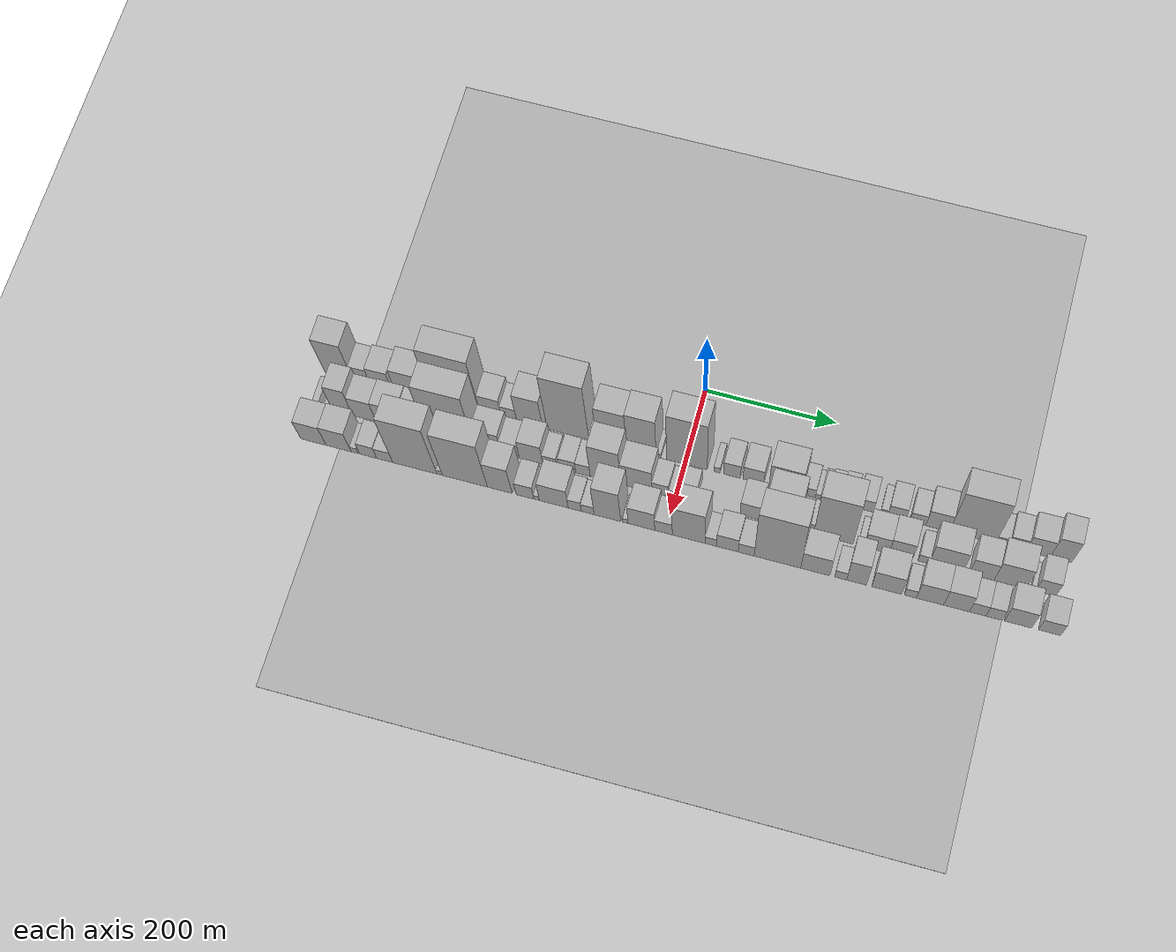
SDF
<?xml version="1.0" encoding="utf-8"?>

<sdf version="1.6">

   <world name="default">

      <gui fullscreen="0">

         <camera name="user_camera">

            <pose>-15 0 4.57585 0 0 0</pose>

            <view_controller>orbit</view_controller>

         </camera>

      </gui>

      <scene>

         <sky>

           <clouds>

             <speed>12</speed>

           </clouds>

         </sky>

         <ambient>0.4 0.4 0.4 1</ambient>

         <background>0.7 0.7 0.7 1</background>

         <shadows>1</shadows>

      </scene>

      <gravity>0 0 -9.8066</gravity>

      <magnetic_field>6e-06 2.3e-05 -4.2e-05</magnetic_field>

      <physics default="0" name="default_physics" type="ode">

         <ode>

            <solver>

               <type>quick</type>

               <iters>10</iters>

               <sor>1.0</sor>

               <use_dynamic_moi_rescaling>0</use_dynamic_moi_rescaling>

            </solver>

            <constraints>

               <cfm>0</cfm>

               <erp>0.2</erp>

               <contact_max_correcting_vel>100</contact_max_correcting_vel>

               <contact_surface_layer>0.001</contact_surface_layer>

            </constraints>

         </ode>

         <max_step_size>0.004</max_step_size>

         <real_time_factor>1</real_time_factor>

         <real_time_update_rate>250</real_time_update_rate>

      </physics>

      <light name="sun" type="directional">

         <cast_shadows>1</cast_shadows>

         <pose>0 0 10 0 0 0</pose>

         <diffuse>0.8 0.8 0.8 1</diffuse>

         <specular>0.2 0.2 0.2 1</specular>

         <attenuation>

            <range>1000</range>

            <constant>0.9</constant>

            <linear>0.01</linear>

            <quadratic>0.001</quadratic>

         </attenuation>

         <direction>-0.5 0.1 -0.9</direction>

      </light>

      <include>

         <name>ground_plane_1</name>

         <uri>model://HANNAS_ground_plane</uri>

         <pose>0 0 0  0 0 0</pose>

      </include>

      <include>

         <name>ground_plane_2</name>

         <uri>model://HANNAS_ground_plane</uri>

         <pose>100 0 0  0 0 0</pose>

      </include>

      <model name="building_1">

         <static>1</static>

         <pose frame="">100.0000 -538.0653 0 0.000000 0.000000 0.000000</pose>

         <link name="link">

            <pose frame="">0 0 63.00 0 0 0</pose>

            <collision name="collision">

               <geometry>

                  <box>

                     <size>40.0000 43.8694 126.0000</size>

                  </box>

               </geometry>

               <max_contacts>10</max_contacts>

               <surface>

                  <contact>

                     <ode/>

                  </contact>

                  <bounce/>

                  <friction>

                     <torsional>

                        <ode/>

                     </torsional>

                     <ode/>

                  </friction>

               </surface>

            </collision>

            <visual name="visual">

               <cast_shadows>0</cast_shadows>

               <geometry>

                  <box>

                     <size>40.0000 43.8694 126.0000</size>

                  </box>

               </geometry>

               <material>

                  <script>

                     <uri>model://HANNAS_wall/materials/scripts</uri>

                     <uri>model://HANNAS_wall/materials/textures</uri>

                     <name>vrc/HANNAS_wall</name>

                  </script>

               </material>

            </visual>

            <self_collide>0</self_collide>

            <enable_wind>0</enable_wind>

            <kinematic>0</kinematic>

         </link>

      </model>

      <model name="building_2">

         <static>1</static>

         <pose frame="">100.0000 -502.6067 0 0.000000 0.000000 0.000000</pose>

         <link name="link">

            <pose frame="">0 0 25.50 0 0 0</pose>

            <collision name="collision">

               <geometry>

                  <box>

                     <size>40.0000 27.0477 51.0000</size>

                  </box>

               </geometry>

               <max_contacts>10</max_contacts>

               <surface>

                  <contact>

                     <ode/>

                  </contact>

                  <bounce/>

                  <friction>

                     <torsional>

                        <ode/>

                     </torsional>

                     <ode/>

                  </friction>

               </surface>

            </collision>

            <visual name="visual">

               <cast_shadows>0</cast_shadows>

               <geometry>

                  <box>

                     <size>40.0000 27.0477 51.0000</size>

                  </box>

               </geometry>

               <material>

                  <script>

                     <uri>model://HANNAS_wall/materials/scripts</uri>

                     <uri>model://HANNAS_wall/materials/textures</uri>

                     <name>vrc/HANNAS_wall</name>

                  </script>

               </material>

            </visual>

            <self_collide>0</self_collide>

            <enable_wind>0</enable_wind>

            <kinematic>0</kinematic>

         </link>

      </model>

      <model name="building_3">

         <static>1</static>

         <pose frame="">100.0000 -472.1858 0 0.000000 0.000000 0.000000</pose>

         <link name="link">

            <pose frame="">0 0 30.00 0 0 0</pose>

            <collision name="collision">

               <geometry>

                  <box>

                     <size>40.0000 33.7942 60.0000</size>

                  </box>

               </geometry>

               <max_contacts>10</max_contacts>

               <surface>

                  <contact>

                     <ode/>

                  </contact>

                  <bounce/>

                  <friction>

                     <torsional>

                        <ode/>

                     </torsional>

                     <ode/>

                  </friction>

               </surface>

            </collision>

            <visual name="visual">

               <cast_shadows>0</cast_shadows>

               <geometry>

                  <box>

                     <size>40.0000 33.7942 60.0000</size>

                  </box>

               </geometry>

               <material>

                  <script>

                     <uri>model://HANNAS_wall/materials/scripts</uri>

                     <uri>model://HANNAS_wall/materials/textures</uri>

                     <name>vrc/HANNAS_wall</name>

                  </script>

               </material>

            </visual>

            <self_collide>0</self_collide>

            <enable_wind>0</enable_wind>

            <kinematic>0</kinematic>

         </link>

      </model>

      <model name="building_4">

         <static>1</static>

         <pose frame="">100.0000 -429.7920 0 0.000000 0.000000 0.000000</pose>

         <link name="link">

            <pose frame="">0 0 39.00 0 0 0</pose>

            <collision name="collision">

               <geometry>

                  <box>

                     <size>40.0000 40.9933 78.0000</size>

                  </box>

               </geometry>

               <max_contacts>10</max_contacts>

               <surface>

                  <contact>

                     <ode/>

                  </contact>

                  <bounce/>

                  <friction>

                     <torsional>

                        <ode/>

                     </torsional>

                     <ode/>

                  </friction>

               </surface>

            </collision>

            <visual name="visual">

               <cast_shadows>0</cast_shadows>

               <geometry>

                  <box>

                     <size>40.0000 40.9933 78.0000</size>

                  </box>

               </geometry>

               <material>

                  <script>

                     <uri>model://HANNAS_wall/materials/scripts</uri>

                     <uri>model://HANNAS_wall/materials/textures</uri>

                     <name>vrc/HANNAS_wall</name>

                  </script>

               </material>

            </visual>

            <self_collide>0</self_collide>

            <enable_wind>0</enable_wind>

            <kinematic>0</kinematic>

         </link>

      </model>

      <model name="building_5">

         <static>1</static>

         <pose frame="">100.0000 -396.8472 0 0.000000 0.000000 0.000000</pose>

         <link name="link">

            <pose frame="">0 0 7.50 0 0 0</pose>

            <collision name="collision">

               <geometry>

                  <box>

                     <size>40.0000 6.8963 15.0000</size>

                  </box>

               </geometry>

               <max_contacts>10</max_contacts>

               <surface>

                  <contact>

                     <ode/>

                  </contact>

                  <bounce/>

                  <friction>

                     <torsional>

                        <ode/>

                     </torsional>

                     <ode/>

                  </friction>

               </surface>

            </collision>

            <visual name="visual">

               <cast_shadows>0</cast_shadows>

               <geometry>

                  <box>

                     <size>40.0000 6.8963 15.0000</size>

                  </box>

               </geometry>

               <material>

                  <script>

                     <uri>model://HANNAS_wall/materials/scripts</uri>

                     <uri>model://HANNAS_wall/materials/textures</uri>

                     <name>vrc/HANNAS_wall</name>

                  </script>

               </material>

            </visual>

            <self_collide>0</self_collide>

            <enable_wind>0</enable_wind>

            <kinematic>0</kinematic>

         </link>

      </model>

      <model name="building_6">

         <static>1</static>

         <pose frame="">100.0000 -355.0737 0 0.000000 0.000000 0.000000</pose>

         <link name="link">

            <pose frame="">0 0 96.00 0 0 0</pose>

            <collision name="collision">

               <geometry>

                  <box>

                     <size>40.0000 76.6506 192.0000</size>

                  </box>

               </geometry>

               <max_contacts>10</max_contacts>

               <surface>

                  <contact>

                     <ode/>

                  </contact>

                  <bounce/>

                  <friction>

                     <torsional>

                        <ode/>

                     </torsional>

                     <ode/>

                  </friction>

               </surface>

            </collision>

            <visual name="visual">

               <cast_shadows>0</cast_shadows>

               <geometry>

                  <box>

                     <size>40.0000 76.6506 192.0000</size>

                  </box>

               </geometry>

               <material>

                  <script>

                     <uri>model://HANNAS_wall/materials/scripts</uri>

                     <uri>model://HANNAS_wall/materials/textures</uri>

                     <name>vrc/HANNAS_wall</name>

                  </script>

               </material>

            </visual>

            <self_collide>0</self_collide>

            <enable_wind>0</enable_wind>

            <kinematic>0</kinematic>

         </link>

      </model>

      <model name="building_7">

         <static>1</static>

         <pose frame="">100.0000 -299.8368 0 0.000000 0.000000 0.000000</pose>

         <link name="link">

            <pose frame="">0 0 33.00 0 0 0</pose>

            <collision name="collision">

               <geometry>

                  <box>

                     <size>40.0000 33.8232 66.0000</size>

                  </box>

               </geometry>

               <max_contacts>10</max_contacts>

               <surface>

                  <contact>

                     <ode/>

                  </contact>

                  <bounce/>

                  <friction>

                     <torsional>

                        <ode/>

                     </torsional>

                     <ode/>

                  </friction>

               </surface>

            </collision>

            <visual name="visual">

               <cast_shadows>0</cast_shadows>

               <geometry>

                  <box>

                     <size>40.0000 33.8232 66.0000</size>

                  </box>

               </geometry>

               <material>

                  <script>

                     <uri>model://HANNAS_wall/materials/scripts</uri>

                     <uri>model://HANNAS_wall/materials/textures</uri>

                     <name>vrc/HANNAS_wall</name>

                  </script>

               </material>

            </visual>

            <self_collide>0</self_collide>

            <enable_wind>0</enable_wind>

            <kinematic>0</kinematic>

         </link>

      </model>

      <model name="building_8">

         <static>1</static>

         <pose frame="">100.0000 -271.1607 0 0.000000 0.000000 0.000000</pose>

         <link name="link">

            <pose frame="">0 0 22.50 0 0 0</pose>

            <collision name="collision">

               <geometry>

                  <box>

                     <size>40.0000 23.5292 45.0000</size>

                  </box>

               </geometry>

               <max_contacts>10</max_contacts>

               <surface>

                  <contact>

                     <ode/>

                  </contact>

                  <bounce/>

                  <friction>

                     <torsional>

                        <ode/>

                     </torsional>

                     <ode/>

                  </friction>

               </surface>

            </collision>

            <visual name="visual">

               <cast_shadows>0</cast_shadows>

               <geometry>

                  <box>

                     <size>40.0000 23.5292 45.0000</size>

                  </box>

               </geometry>

               <material>

                  <script>

                     <uri>model://HANNAS_wall/materials/scripts</uri>

                     <uri>model://HANNAS_wall/materials/textures</uri>

                     <name>vrc/HANNAS_wall</name>

                  </script>

               </material>

            </visual>

            <self_collide>0</self_collide>

            <enable_wind>0</enable_wind>

            <kinematic>0</kinematic>

         </link>

      </model>

      <model name="building_9">

         <static>1</static>

         <pose frame="">100.0000 -239.2058 0 0.000000 0.000000 0.000000</pose>

         <link name="link">

            <pose frame="">0 0 52.50 0 0 0</pose>

            <collision name="collision">

               <geometry>

                  <box>

                     <size>40.0000 40.3806 105.0000</size>

                  </box>

               </geometry>

               <max_contacts>10</max_contacts>

               <surface>

                  <contact>

                     <ode/>

                  </contact>

                  <bounce/>

                  <friction>

                     <torsional>

                        <ode/>

                     </torsional>

                     <ode/>

                  </friction>

               </surface>

            </collision>

            <visual name="visual">

               <cast_shadows>0</cast_shadows>

               <geometry>

                  <box>

                     <size>40.0000 40.3806 105.0000</size>

                  </box>

               </geometry>

               <material>

                  <script>

                     <uri>model://HANNAS_wall/materials/scripts</uri>

                     <uri>model://HANNAS_wall/materials/textures</uri>

                     <name>vrc/HANNAS_wall</name>

                  </script>

               </material>

            </visual>

            <self_collide>0</self_collide>

            <enable_wind>0</enable_wind>

            <kinematic>0</kinematic>

         </link>

      </model>

      <model name="building_10">

         <static>1</static>

         <pose frame="">100.0000 -179.8316 0 0.000000 0.000000 0.000000</pose>

         <link name="link">

            <pose frame="">0 0 103.50 0 0 0</pose>

            <collision name="collision">

               <geometry>

                  <box>

                     <size>40.0000 64.3677 207.0000</size>

                  </box>

               </geometry>

               <max_contacts>10</max_contacts>

               <surface>

                  <contact>

                     <ode/>

                  </contact>

                  <bounce/>

                  <friction>

                     <torsional>

                        <ode/>

                     </torsional>

                     <ode/>

                  </friction>

               </surface>

            </collision>

            <visual name="visual">

               <cast_shadows>0</cast_shadows>

               <geometry>

                  <box>

                     <size>40.0000 64.3677 207.0000</size>

                  </box>

               </geometry>

               <material>

                  <script>

                     <uri>model://HANNAS_wall/materials/scripts</uri>

                     <uri>model://HANNAS_wall/materials/textures</uri>

                     <name>vrc/HANNAS_wall</name>

                  </script>

               </material>

            </visual>

            <self_collide>0</self_collide>

            <enable_wind>0</enable_wind>

            <kinematic>0</kinematic>

         </link>

      </model>

      <model name="building_11">

         <static>1</static>

         <pose frame="">100.0000 -141.6999 0 0.000000 0.000000 0.000000</pose>

         <link name="link">

            <pose frame="">0 0 12.00 0 0 0</pose>

            <collision name="collision">

               <geometry>

                  <box>

                     <size>40.0000 11.8957 24.0000</size>

                  </box>

               </geometry>

               <max_contacts>10</max_contacts>

               <surface>

                  <contact>

                     <ode/>

                  </contact>

                  <bounce/>

                  <friction>

                     <torsional>

                        <ode/>

                     </torsional>

                     <ode/>

                  </friction>

               </surface>

            </collision>

            <visual name="visual">

               <cast_shadows>0</cast_shadows>

               <geometry>

                  <box>

                     <size>40.0000 11.8957 24.0000</size>

                  </box>

               </geometry>

               <material>

                  <script>

                     <uri>model://HANNAS_wall/materials/scripts</uri>

                     <uri>model://HANNAS_wall/materials/textures</uri>

                     <name>vrc/HANNAS_wall</name>

                  </script>

               </material>

            </visual>

            <self_collide>0</self_collide>

            <enable_wind>0</enable_wind>

            <kinematic>0</kinematic>

         </link>

      </model>

      <model name="building_12">

         <static>1</static>

         <pose frame="">100.0000 -112.7163 0 0.000000 0.000000 0.000000</pose>

         <link name="link">

            <pose frame="">0 0 69.00 0 0 0</pose>

            <collision name="collision">

               <geometry>

                  <box>

                     <size>40.0000 46.0715 138.0000</size>

                  </box>

               </geometry>

               <max_contacts>10</max_contacts>

               <surface>

                  <contact>

                     <ode/>

                  </contact>

                  <bounce/>

                  <friction>

                     <torsional>

                        <ode/>

                     </torsional>

                     <ode/>

                  </friction>

               </surface>

            </collision>

            <visual name="visual">

               <cast_shadows>0</cast_shadows>

               <geometry>

                  <box>

                     <size>40.0000 46.0715 138.0000</size>

                  </box>

               </geometry>

               <material>

                  <script>

                     <uri>model://HANNAS_wall/materials/scripts</uri>

                     <uri>model://HANNAS_wall/materials/textures</uri>

                     <name>vrc/HANNAS_wall</name>

                  </script>

               </material>

            </visual>

            <self_collide>0</self_collide>

            <enable_wind>0</enable_wind>

            <kinematic>0</kinematic>

         </link>

      </model>

      <model name="building_13">

         <static>1</static>

         <pose frame="">100.0000 -67.0295 0 0.000000 0.000000 0.000000</pose>

         <link name="link">

            <pose frame="">0 0 72.00 0 0 0</pose>

            <collision name="collision">

               <geometry>

                  <box>

                     <size>40.0000 45.3021 144.0000</size>

                  </box>

               </geometry>

               <max_contacts>10</max_contacts>

               <surface>

                  <contact>

                     <ode/>

                  </contact>

                  <bounce/>

                  <friction>

                     <torsional>

                        <ode/>

                     </torsional>

                     <ode/>

                  </friction>

               </surface>

            </collision>

            <visual name="visual">

               <cast_shadows>0</cast_shadows>

               <geometry>

                  <box>

                     <size>40.0000 45.3021 144.0000</size>

                  </box>

               </geometry>

               <material>

                  <script>

                     <uri>model://HANNAS_wall/materials/scripts</uri>

                     <uri>model://HANNAS_wall/materials/textures</uri>

                     <name>vrc/HANNAS_wall</name>

                  </script>

               </material>

            </visual>

            <self_collide>0</self_collide>

            <enable_wind>0</enable_wind>

            <kinematic>0</kinematic>

         </link>

      </model>

      <model name="building_14">

         <static>1</static>

         <pose frame="">100.0000 -40.6850 0 0.000000 0.000000 0.000000</pose>

         <link name="link">

            <pose frame="">0 0 7.50 0 0 0</pose>

            <collision name="collision">

               <geometry>

                  <box>

                     <size>40.0000 7.3868 15.0000</size>

                  </box>

               </geometry>

               <max_contacts>10</max_contacts>

               <surface>

                  <contact>

                     <ode/>

                  </contact>

                  <bounce/>

                  <friction>

                     <torsional>

                        <ode/>

                     </torsional>

                     <ode/>

                  </friction>

               </surface>

            </collision>

            <visual name="visual">

               <cast_shadows>0</cast_shadows>

               <geometry>

                  <box>

                     <size>40.0000 7.3868 15.0000</size>

                  </box>

               </geometry>

               <material>

                  <script>

                     <uri>model://HANNAS_wall/materials/scripts</uri>

                     <uri>model://HANNAS_wall/materials/textures</uri>

                     <name>vrc/HANNAS_wall</name>

                  </script>

               </material>

            </visual>

            <self_collide>0</self_collide>

            <enable_wind>0</enable_wind>

            <kinematic>0</kinematic>

         </link>

      </model>

      <model name="building_15">

         <static>1</static>

         <pose frame="">100.0000 2.7650 0 0.000000 0.000000 0.000000</pose>

         <link name="link">

            <pose frame="">0 0 91.50 0 0 0</pose>

            <collision name="collision">

               <geometry>

                  <box>

                     <size>40.0000 61.5131 183.0000</size>

                  </box>

               </geometry>

               <max_contacts>10</max_contacts>

               <surface>

                  <contact>

                     <ode/>

                  </contact>

                  <bounce/>

                  <friction>

                     <torsional>

                        <ode/>

                     </torsional>

                     <ode/>

                  </friction>

               </surface>

            </collision>

            <visual name="visual">

               <cast_shadows>0</cast_shadows>

               <geometry>

                  <box>

                     <size>40.0000 61.5131 183.0000</size>

                  </box>

               </geometry>

               <material>

                  <script>

                     <uri>model://HANNAS_wall/materials/scripts</uri>

                     <uri>model://HANNAS_wall/materials/textures</uri>

                     <name>vrc/HANNAS_wall</name>

                  </script>

               </material>

            </visual>

            <self_collide>0</self_collide>

            <enable_wind>0</enable_wind>

            <kinematic>0</kinematic>

         </link>

      </model>

      <model name="building_16">

         <static>1</static>

         <pose frame="">100.0000 48.4366 0 0.000000 0.000000 0.000000</pose>

         <link name="link">

            <pose frame="">0 0 10.50 0 0 0</pose>

            <collision name="collision">

               <geometry>

                  <box>

                     <size>40.0000 9.8300 21.0000</size>

                  </box>

               </geometry>

               <max_contacts>10</max_contacts>

               <surface>

                  <contact>

                     <ode/>

                  </contact>

                  <bounce/>

                  <friction>

                     <torsional>

                        <ode/>

                     </torsional>

                     <ode/>

                  </friction>

               </surface>

            </collision>

            <visual name="visual">

               <cast_shadows>0</cast_shadows>

               <geometry>

                  <box>

                     <size>40.0000 9.8300 21.0000</size>

                  </box>

               </geometry>

               <material>

                  <script>

                     <uri>model://HANNAS_wall/materials/scripts</uri>

                     <uri>model://HANNAS_wall/materials/textures</uri>

                     <name>vrc/HANNAS_wall</name>

                  </script>

               </material>

            </visual>

            <self_collide>0</self_collide>

            <enable_wind>0</enable_wind>

            <kinematic>0</kinematic>

         </link>

      </model>

      <model name="building_17">

         <static>1</static>

         <pose frame="">100.0000 71.2778 0 0.000000 0.000000 0.000000</pose>

         <link name="link">

            <pose frame="">0 0 25.50 0 0 0</pose>

            <collision name="collision">

               <geometry>

                  <box>

                     <size>40.0000 25.8524 51.0000</size>

                  </box>

               </geometry>

               <max_contacts>10</max_contacts>

               <surface>

                  <contact>

                     <ode/>

                  </contact>

                  <bounce/>

                  <friction>

                     <torsional>

                        <ode/>

                     </torsional>

                     <ode/>

                  </friction>

               </surface>

            </collision>

            <visual name="visual">

               <cast_shadows>0</cast_shadows>

               <geometry>

                  <box>

                     <size>40.0000 25.8524 51.0000</size>

                  </box>

               </geometry>

               <material>

                  <script>

                     <uri>model://HANNAS_wall/materials/scripts</uri>

                     <uri>model://HANNAS_wall/materials/textures</uri>

                     <name>vrc/HANNAS_wall</name>

                  </script>

               </material>

            </visual>

            <self_collide>0</self_collide>

            <enable_wind>0</enable_wind>

            <kinematic>0</kinematic>

         </link>

      </model>

      <model name="building_18">

         <static>1</static>

         <pose frame="">100.0000 103.9225 0 0.000000 0.000000 0.000000</pose>

         <link name="link">

            <pose frame="">0 0 27.00 0 0 0</pose>

            <collision name="collision">

               <geometry>

                  <box>

                     <size>40.0000 31.4371 54.0000</size>

                  </box>

               </geometry>

               <max_contacts>10</max_contacts>

               <surface>

                  <contact>

                     <ode/>

                  </contact>

                  <bounce/>

                  <friction>

                     <torsional>

                        <ode/>

                     </torsional>

                     <ode/>

                  </friction>

               </surface>

            </collision>

            <visual name="visual">

               <cast_shadows>0</cast_shadows>

               <geometry>

                  <box>

                     <size>40.0000 31.4371 54.0000</size>

                  </box>

               </geometry>

               <material>

                  <script>

                     <uri>model://HANNAS_wall/materials/scripts</uri>

                     <uri>model://HANNAS_wall/materials/textures</uri>

                     <name>vrc/HANNAS_wall</name>

                  </script>

               </material>

            </visual>

            <self_collide>0</self_collide>

            <enable_wind>0</enable_wind>

            <kinematic>0</kinematic>

         </link>

      </model>

      <model name="building_19">

         <static>1</static>

         <pose frame="">100.0000 152.8931 0 0.000000 0.000000 0.000000</pose>

         <link name="link">

            <pose frame="">0 0 45.00 0 0 0</pose>

            <collision name="collision">

               <geometry>

                  <box>

                     <size>40.0000 50.5041 90.0000</size>

                  </box>

               </geometry>

               <max_contacts>10</max_contacts>

               <surface>

                  <contact>

                     <ode/>

                  </contact>

                  <bounce/>

                  <friction>

                     <torsional>

                        <ode/>

                     </torsional>

                     <ode/>

                  </friction>

               </surface>

            </collision>

            <visual name="visual">

               <cast_shadows>0</cast_shadows>

               <geometry>

                  <box>

                     <size>40.0000 50.5041 90.0000</size>

                  </box>

               </geometry>

               <material>

                  <script>

                     <uri>model://HANNAS_wall/materials/scripts</uri>

                     <uri>model://HANNAS_wall/materials/textures</uri>

                     <name>vrc/HANNAS_wall</name>

                  </script>

               </material>

            </visual>

            <self_collide>0</self_collide>

            <enable_wind>0</enable_wind>

            <kinematic>0</kinematic>

         </link>

      </model>

      <model name="building_20">

         <static>1</static>

         <pose frame="">100.0000 187.9797 0 0.000000 0.000000 0.000000</pose>

         <link name="link">

            <pose frame="">0 0 16.50 0 0 0</pose>

            <collision name="collision">

               <geometry>

                  <box>

                     <size>40.0000 19.6692 33.0000</size>

                  </box>

               </geometry>

               <max_contacts>10</max_contacts>

               <surface>

                  <contact>

                     <ode/>

                  </contact>

                  <bounce/>

                  <friction>

                     <torsional>

                        <ode/>

                     </torsional>

                     <ode/>

                  </friction>

               </surface>

            </collision>

            <visual name="visual">

               <cast_shadows>0</cast_shadows>

               <geometry>

                  <box>

                     <size>40.0000 19.6692 33.0000</size>

                  </box>

               </geometry>

               <material>

                  <script>

                     <uri>model://HANNAS_wall/materials/scripts</uri>

                     <uri>model://HANNAS_wall/materials/textures</uri>

                     <name>vrc/HANNAS_wall</name>

                  </script>

               </material>

            </visual>

            <self_collide>0</self_collide>

            <enable_wind>0</enable_wind>

            <kinematic>0</kinematic>

         </link>

      </model>

      <model name="building_21">

         <static>1</static>

         <pose frame="">100.0000 201.5192 0 0.000000 0.000000 0.000000</pose>

         <link name="link">

            <pose frame="">0 0 7.50 0 0 0</pose>

            <collision name="collision">

               <geometry>

                  <box>

                     <size>40.0000 7.4098 15.0000</size>

                  </box>

               </geometry>

               <max_contacts>10</max_contacts>

               <surface>

                  <contact>

                     <ode/>

                  </contact>

                  <bounce/>

                  <friction>

                     <torsional>

                        <ode/>

                     </torsional>

                     <ode/>

                  </friction>

               </surface>

            </collision>

            <visual name="visual">

               <cast_shadows>0</cast_shadows>

               <geometry>

                  <box>

                     <size>40.0000 7.4098 15.0000</size>

                  </box>

               </geometry>

               <material>

                  <script>

                     <uri>model://HANNAS_wall/materials/scripts</uri>

                     <uri>model://HANNAS_wall/materials/textures</uri>

                     <name>vrc/HANNAS_wall</name>

                  </script>

               </material>

            </visual>

            <self_collide>0</self_collide>

            <enable_wind>0</enable_wind>

            <kinematic>0</kinematic>

         </link>

      </model>

      <model name="building_22">

         <static>1</static>

         <pose frame="">100.0000 210.9200 0 0.000000 0.000000 0.000000</pose>

         <link name="link">

            <pose frame="">0 0 13.50 0 0 0</pose>

            <collision name="collision">

               <geometry>

                  <box>

                     <size>40.0000 11.3917 27.0000</size>

                  </box>

               </geometry>

               <max_contacts>10</max_contacts>

               <surface>

                  <contact>

                     <ode/>

                  </contact>

                  <bounce/>

                  <friction>

                     <torsional>

                        <ode/>

                     </torsional>

                     <ode/>

                  </friction>

               </surface>

            </collision>

            <visual name="visual">

               <cast_shadows>0</cast_shadows>

               <geometry>

                  <box>

                     <size>40.0000 11.3917 27.0000</size>

                  </box>

               </geometry>

               <material>

                  <script>

                     <uri>model://HANNAS_wall/materials/scripts</uri>

                     <uri>model://HANNAS_wall/materials/textures</uri>

                     <name>vrc/HANNAS_wall</name>

                  </script>

               </material>

            </visual>

            <self_collide>0</self_collide>

            <enable_wind>0</enable_wind>

            <kinematic>0</kinematic>

         </link>

      </model>

      <model name="building_23">

         <static>1</static>

         <pose frame="">100.0000 226.0352 0 0.000000 0.000000 0.000000</pose>

         <link name="link">

            <pose frame="">0 0 16.50 0 0 0</pose>

            <collision name="collision">

               <geometry>

                  <box>

                     <size>40.0000 18.8387 33.0000</size>

                  </box>

               </geometry>

               <max_contacts>10</max_contacts>

               <surface>

                  <contact>

                     <ode/>

                  </contact>

                  <bounce/>

                  <friction>

                     <torsional>

                        <ode/>

                     </torsional>

                     <ode/>

                  </friction>

               </surface>

            </collision>

            <visual name="visual">

               <cast_shadows>0</cast_shadows>

               <geometry>

                  <box>

                     <size>40.0000 18.8387 33.0000</size>

                  </box>

               </geometry>

               <material>

                  <script>

                     <uri>model://HANNAS_wall/materials/scripts</uri>

                     <uri>model://HANNAS_wall/materials/textures</uri>

                     <name>vrc/HANNAS_wall</name>

                  </script>

               </material>

            </visual>

            <self_collide>0</self_collide>

            <enable_wind>0</enable_wind>

            <kinematic>0</kinematic>

         </link>

      </model>

      <model name="building_24">

         <static>1</static>

         <pose frame="">100.0000 246.1372 0 0.000000 0.000000 0.000000</pose>

         <link name="link">

            <pose frame="">0 0 19.50 0 0 0</pose>

            <collision name="collision">

               <geometry>

                  <box>

                     <size>40.0000 21.3654 39.0000</size>

                  </box>

               </geometry>

               <max_contacts>10</max_contacts>

               <surface>

                  <contact>

                     <ode/>

                  </contact>

                  <bounce/>

                  <friction>

                     <torsional>

                        <ode/>

                     </torsional>

                     <ode/>

                  </friction>

               </surface>

            </collision>

            <visual name="visual">

               <cast_shadows>0</cast_shadows>

               <geometry>

                  <box>

                     <size>40.0000 21.3654 39.0000</size>

                  </box>

               </geometry>

               <material>

                  <script>

                     <uri>model://HANNAS_wall/materials/scripts</uri>

                     <uri>model://HANNAS_wall/materials/textures</uri>

                     <name>vrc/HANNAS_wall</name>

                  </script>

               </material>

            </visual>

            <self_collide>0</self_collide>

            <enable_wind>0</enable_wind>

            <kinematic>0</kinematic>

         </link>

      </model>

      <model name="building_25">

         <static>1</static>

         <pose frame="">100.0000 273.0623 0 0.000000 0.000000 0.000000</pose>

         <link name="link">

            <pose frame="">0 0 22.50 0 0 0</pose>

            <collision name="collision">

               <geometry>

                  <box>

                     <size>40.0000 24.4847 45.0000</size>

                  </box>

               </geometry>

               <max_contacts>10</max_contacts>

               <surface>

                  <contact>

                     <ode/>

                  </contact>

                  <bounce/>

                  <friction>

                     <torsional>

                        <ode/>

                     </torsional>

                     <ode/>

                  </friction>

               </surface>

            </collision>

            <visual name="visual">

               <cast_shadows>0</cast_shadows>

               <geometry>

                  <box>

                     <size>40.0000 24.4847 45.0000</size>

                  </box>

               </geometry>

               <material>

                  <script>

                     <uri>model://HANNAS_wall/materials/scripts</uri>

                     <uri>model://HANNAS_wall/materials/textures</uri>

                     <name>vrc/HANNAS_wall</name>

                  </script>

               </material>

            </visual>

            <self_collide>0</self_collide>

            <enable_wind>0</enable_wind>

            <kinematic>0</kinematic>

         </link>

      </model>

      <model name="building_26">

         <static>1</static>

         <pose frame="">100.0000 300.9104 0 0.000000 0.000000 0.000000</pose>

         <link name="link">

            <pose frame="">0 0 12.00 0 0 0</pose>

            <collision name="collision">

               <geometry>

                  <box>

                     <size>40.0000 11.2115 24.0000</size>

                  </box>

               </geometry>

               <max_contacts>10</max_contacts>

               <surface>

                  <contact>

                     <ode/>

                  </contact>

                  <bounce/>

                  <friction>

                     <torsional>

                        <ode/>

                     </torsional>

                     <ode/>

                  </friction>

               </surface>

            </collision>

            <visual name="visual">

               <cast_shadows>0</cast_shadows>

               <geometry>

                  <box>

                     <size>40.0000 11.2115 24.0000</size>

                  </box>

               </geometry>

               <material>

                  <script>

                     <uri>model://HANNAS_wall/materials/scripts</uri>

                     <uri>model://HANNAS_wall/materials/textures</uri>

                     <name>vrc/HANNAS_wall</name>

                  </script>

               </material>

            </visual>

            <self_collide>0</self_collide>

            <enable_wind>0</enable_wind>

            <kinematic>0</kinematic>

         </link>

      </model>

      <model name="building_27">

         <static>1</static>

         <pose frame="">100.0000 320.0140 0 0.000000 0.000000 0.000000</pose>

         <link name="link">

            <pose frame="">0 0 24.00 0 0 0</pose>

            <collision name="collision">

               <geometry>

                  <box>

                     <size>40.0000 26.9957 48.0000</size>

                  </box>

               </geometry>

               <max_contacts>10</max_contacts>

               <surface>

                  <contact>

                     <ode/>

                  </contact>

                  <bounce/>

                  <friction>

                     <torsional>

                        <ode/>

                     </torsional>

                     <ode/>

                  </friction>

               </surface>

            </collision>

            <visual name="visual">

               <cast_shadows>0</cast_shadows>

               <geometry>

                  <box>

                     <size>40.0000 26.9957 48.0000</size>

                  </box>

               </geometry>

               <material>

                  <script>

                     <uri>model://HANNAS_wall/materials/scripts</uri>

                     <uri>model://HANNAS_wall/materials/textures</uri>

                     <name>vrc/HANNAS_wall</name>

                  </script>

               </material>

            </visual>

            <self_collide>0</self_collide>

            <enable_wind>0</enable_wind>

            <kinematic>0</kinematic>

         </link>

      </model>

      <model name="building_28">

         <static>1</static>

         <pose frame="">100.0000 351.4350 0 0.000000 0.000000 0.000000</pose>

         <link name="link">

            <pose frame="">0 0 21.00 0 0 0</pose>

            <collision name="collision">

               <geometry>

                  <box>

                     <size>40.0000 23.8461 42.0000</size>

                  </box>

               </geometry>

               <max_contacts>10</max_contacts>

               <surface>

                  <contact>

                     <ode/>

                  </contact>

                  <bounce/>

                  <friction>

                     <torsional>

                        <ode/>

                     </torsional>

                     <ode/>

                  </friction>

               </surface>

            </collision>

            <visual name="visual">

               <cast_shadows>0</cast_shadows>

               <geometry>

                  <box>

                     <size>40.0000 23.8461 42.0000</size>

                  </box>

               </geometry>

               <material>

                  <script>

                     <uri>model://HANNAS_wall/materials/scripts</uri>

                     <uri>model://HANNAS_wall/materials/textures</uri>

                     <name>vrc/HANNAS_wall</name>

                  </script>

               </material>

            </visual>

            <self_collide>0</self_collide>

            <enable_wind>0</enable_wind>

            <kinematic>0</kinematic>

         </link>

      </model>

      <model name="building_29">

         <static>1</static>

         <pose frame="">100.0000 381.1314 0 0.000000 0.000000 0.000000</pose>

         <link name="link">

            <pose frame="">0 0 34.50 0 0 0</pose>

            <collision name="collision">

               <geometry>

                  <box>

                     <size>40.0000 35.5467 69.0000</size>

                  </box>

               </geometry>

               <max_contacts>10</max_contacts>

               <surface>

                  <contact>

                     <ode/>

                  </contact>

                  <bounce/>

                  <friction>

                     <torsional>

                        <ode/>

                     </torsional>

                     <ode/>

                  </friction>

               </surface>

            </collision>

            <visual name="visual">

               <cast_shadows>0</cast_shadows>

               <geometry>

                  <box>

                     <size>40.0000 35.5467 69.0000</size>

                  </box>

               </geometry>

               <material>

                  <script>

                     <uri>model://HANNAS_wall/materials/scripts</uri>

                     <uri>model://HANNAS_wall/materials/textures</uri>

                     <name>vrc/HANNAS_wall</name>

                  </script>

               </material>

            </visual>

            <self_collide>0</self_collide>

            <enable_wind>0</enable_wind>

            <kinematic>0</kinematic>

         </link>

      </model>

      <model name="building_30">

         <static>1</static>

         <pose frame="">100.0000 433.1058 0 0.000000 0.000000 0.000000</pose>

         <link name="link">

            <pose frame="">0 0 88.50 0 0 0</pose>

            <collision name="collision">

               <geometry>

                  <box>

                     <size>40.0000 68.4021 177.0000</size>

                  </box>

               </geometry>

               <max_contacts>10</max_contacts>

               <surface>

                  <contact>

                     <ode/>

                  </contact>

                  <bounce/>

                  <friction>

                     <torsional>

                        <ode/>

                     </torsional>

                     <ode/>

                  </friction>

               </surface>

            </collision>

            <visual name="visual">

               <cast_shadows>0</cast_shadows>

               <geometry>

                  <box>

                     <size>40.0000 68.4021 177.0000</size>

                  </box>

               </geometry>

               <material>

                  <script>

                     <uri>model://HANNAS_wall/materials/scripts</uri>

                     <uri>model://HANNAS_wall/materials/textures</uri>

                     <name>vrc/HANNAS_wall</name>

                  </script>

               </material>

            </visual>

            <self_collide>0</self_collide>

            <enable_wind>0</enable_wind>

            <kinematic>0</kinematic>

         </link>

      </model>

      <model name="building_31">

         <static>1</static>

         <pose frame="">100.0000 476.4380 0 0.000000 0.000000 0.000000</pose>

         <link name="link">

            <pose frame="">0 0 16.50 0 0 0</pose>

            <collision name="collision">

               <geometry>

                  <box>

                     <size>40.0000 18.2624 33.0000</size>

                  </box>

               </geometry>

               <max_contacts>10</max_contacts>

               <surface>

                  <contact>

                     <ode/>

                  </contact>

                  <bounce/>

                  <friction>

                     <torsional>

                        <ode/>

                     </torsional>

                     <ode/>

                  </friction>

               </surface>

            </collision>

            <visual name="visual">

               <cast_shadows>0</cast_shadows>

               <geometry>

                  <box>

                     <size>40.0000 18.2624 33.0000</size>

                  </box>

               </geometry>

               <material>

                  <script>

                     <uri>model://HANNAS_wall/materials/scripts</uri>

                     <uri>model://HANNAS_wall/materials/textures</uri>

                     <name>vrc/HANNAS_wall</name>

                  </script>

               </material>

            </visual>

            <self_collide>0</self_collide>

            <enable_wind>0</enable_wind>

            <kinematic>0</kinematic>

         </link>

      </model>

      <model name="building_32">

         <static>1</static>

         <pose frame="">100.0000 498.9641 0 0.000000 0.000000 0.000000</pose>

         <link name="link">

            <pose frame="">0 0 24.00 0 0 0</pose>

            <collision name="collision">

               <geometry>

                  <box>

                     <size>40.0000 26.7897 48.0000</size>

                  </box>

               </geometry>

               <max_contacts>10</max_contacts>

               <surface>

                  <contact>

                     <ode/>

                  </contact>

                  <bounce/>

                  <friction>

                     <torsional>

                        <ode/>

                     </torsional>

                     <ode/>

                  </friction>

               </surface>

            </collision>

            <visual name="visual">

               <cast_shadows>0</cast_shadows>

               <geometry>

                  <box>

                     <size>40.0000 26.7897 48.0000</size>

                  </box>

               </geometry>

               <material>

                  <script>

                     <uri>model://HANNAS_wall/materials/scripts</uri>

                     <uri>model://HANNAS_wall/materials/textures</uri>

                     <name>vrc/HANNAS_wall</name>

                  </script>

               </material>

            </visual>

            <self_collide>0</self_collide>

            <enable_wind>0</enable_wind>

            <kinematic>0</kinematic>

         </link>

      </model>

      <model name="building_33">

         <static>1</static>

         <pose frame="">100.0000 530.1919 0 0.000000 0.000000 0.000000</pose>

         <link name="link">

            <pose frame="">0 0 34.50 0 0 0</pose>

            <collision name="collision">

               <geometry>

                  <box>

                     <size>40.0000 35.6658 69.0000</size>

                  </box>

               </geometry>

               <max_contacts>10</max_contacts>

               <surface>

                  <contact>

                     <ode/>

                  </contact>

                  <bounce/>

                  <friction>

                     <torsional>

                        <ode/>

                     </torsional>

                     <ode/>

                  </friction>

               </surface>

            </collision>

            <visual name="visual">

               <cast_shadows>0</cast_shadows>

               <geometry>

                  <box>

                     <size>40.0000 35.6658 69.0000</size>

                  </box>

               </geometry>

               <material>

                  <script>

                     <uri>model://HANNAS_wall/materials/scripts</uri>

                     <uri>model://HANNAS_wall/materials/textures</uri>

                     <name>vrc/HANNAS_wall</name>

                  </script>

               </material>

            </visual>

            <self_collide>0</self_collide>

            <enable_wind>0</enable_wind>

            <kinematic>0</kinematic>

         </link>

      </model>

      <model name="building_34">

         <static>1</static>

         <pose frame="">100.0000 563.8927 0 0.000000 0.000000 0.000000</pose>

         <link name="link">

            <pose frame="">0 0 46.50 0 0 0</pose>

            <collision name="collision">

               <geometry>

                  <box>

                     <size>40.0000 31.7359 93.0000</size>

                  </box>

               </geometry>

               <max_contacts>10</max_contacts>

               <surface>

                  <contact>

                     <ode/>

                  </contact>

                  <bounce/>

                  <friction>

                     <torsional>

                        <ode/>

                     </torsional>

                     <ode/>

                  </friction>

               </surface>

            </collision>

            <visual name="visual">

               <cast_shadows>0</cast_shadows>

               <geometry>

                  <box>

                     <size>40.0000 31.7359 93.0000</size>

                  </box>

               </geometry>

               <material>

                  <script>

                     <uri>model://HANNAS_wall/materials/scripts</uri>

                     <uri>model://HANNAS_wall/materials/textures</uri>

                     <name>vrc/HANNAS_wall</name>

                  </script>

               </material>

            </visual>

            <self_collide>0</self_collide>

            <enable_wind>0</enable_wind>

            <kinematic>0</kinematic>

         </link>

      </model>

      <model name="building_35">

         <static>1</static>

         <pose frame="">155.0000 -551.8462 0 0.000000 0.000000 0.000000</pose>

         <link name="link">

            <pose frame="">0 0 12.00 0 0 0</pose>

            <collision name="collision">

               <geometry>

                  <box>

                     <size>40.0000 10.3077 24.0000</size>

                  </box>

               </geometry>

               <max_contacts>10</max_contacts>

               <surface>

                  <contact>

                     <ode/>

                  </contact>

                  <bounce/>

                  <friction>

                     <torsional>

                        <ode/>

                     </torsional>

                     <ode/>

                  </friction>

               </surface>

            </collision>

            <visual name="visual">

               <cast_shadows>0</cast_shadows>

               <geometry>

                  <box>

                     <size>40.0000 10.3077 24.0000</size>

                  </box>

               </geometry>

               <material>

                  <script>

                     <uri>model://HANNAS_wall/materials/scripts</uri>

                     <uri>model://HANNAS_wall/materials/textures</uri>

                     <name>vrc/HANNAS_wall</name>

                  </script>

               </material>

            </visual>

            <self_collide>0</self_collide>

            <enable_wind>0</enable_wind>

            <kinematic>0</kinematic>

         </link>

      </model>

      <model name="building_36">

         <static>1</static>

         <pose frame="">155.0000 -533.7360 0 0.000000 0.000000 0.000000</pose>

         <link name="link">

            <pose frame="">0 0 10.50 0 0 0</pose>

            <collision name="collision">

               <geometry>

                  <box>

                     <size>40.0000 9.9126 21.0000</size>

                  </box>

               </geometry>

               <max_contacts>10</max_contacts>

               <surface>

                  <contact>

                     <ode/>

                  </contact>

                  <bounce/>

                  <friction>

                     <torsional>

                        <ode/>

                     </torsional>

                     <ode/>

                  </friction>

               </surface>

            </collision>

            <visual name="visual">

               <cast_shadows>0</cast_shadows>

               <geometry>

                  <box>

                     <size>40.0000 9.9126 21.0000</size>

                  </box>

               </geometry>

               <material>

                  <script>

                     <uri>model://HANNAS_wall/materials/scripts</uri>

                     <uri>model://HANNAS_wall/materials/textures</uri>

                     <name>vrc/HANNAS_wall</name>

                  </script>

               </material>

            </visual>

            <self_collide>0</self_collide>

            <enable_wind>0</enable_wind>

            <kinematic>0</kinematic>

         </link>

      </model>

      <model name="building_37">

         <static>1</static>

         <pose frame="">155.0000 -513.0303 0 0.000000 0.000000 0.000000</pose>

         <link name="link">

            <pose frame="">0 0 48.00 0 0 0</pose>

            <collision name="collision">

               <geometry>

                  <box>

                     <size>40.0000 31.4988 96.0000</size>

                  </box>

               </geometry>

               <max_contacts>10</max_contacts>

               <surface>

                  <contact>

                     <ode/>

                  </contact>

                  <bounce/>

                  <friction>

                     <torsional>

                        <ode/>

                     </torsional>

                     <ode/>

                  </friction>

               </surface>

            </collision>

            <visual name="visual">

               <cast_shadows>0</cast_shadows>

               <geometry>

                  <box>

                     <size>40.0000 31.4988 96.0000</size>

                  </box>

               </geometry>

               <material>

                  <script>

                     <uri>model://HANNAS_wall/materials/scripts</uri>

                     <uri>model://HANNAS_wall/materials/textures</uri>

                     <name>vrc/HANNAS_wall</name>

                  </script>

               </material>

            </visual>

            <self_collide>0</self_collide>

            <enable_wind>0</enable_wind>

            <kinematic>0</kinematic>

         </link>

      </model>

      <model name="building_38">

         <static>1</static>

         <pose frame="">155.0000 -479.1064 0 0.000000 0.000000 0.000000</pose>

         <link name="link">

            <pose frame="">0 0 36.00 0 0 0</pose>

            <collision name="collision">

               <geometry>

                  <box>

                     <size>40.0000 36.3490 72.0000</size>

                  </box>

               </geometry>

               <max_contacts>10</max_contacts>

               <surface>

                  <contact>

                     <ode/>

                  </contact>

                  <bounce/>

                  <friction>

                     <torsional>

                        <ode/>

                     </torsional>

                     <ode/>

                  </friction>

               </surface>

            </collision>

            <visual name="visual">

               <cast_shadows>0</cast_shadows>

               <geometry>

                  <box>

                     <size>40.0000 36.3490 72.0000</size>

                  </box>

               </geometry>

               <material>

                  <script>

                     <uri>model://HANNAS_wall/materials/scripts</uri>

                     <uri>model://HANNAS_wall/materials/textures</uri>

                     <name>vrc/HANNAS_wall</name>

                  </script>

               </material>

            </visual>

            <self_collide>0</self_collide>

            <enable_wind>0</enable_wind>

            <kinematic>0</kinematic>

         </link>

      </model>

      <model name="building_39">

         <static>1</static>

         <pose frame="">155.0000 -440.3385 0 0.000000 0.000000 0.000000</pose>

         <link name="link">

            <pose frame="">0 0 37.50 0 0 0</pose>

            <collision name="collision">

               <geometry>

                  <box>

                     <size>40.0000 41.1868 75.0000</size>

                  </box>

               </geometry>

               <max_contacts>10</max_contacts>

               <surface>

                  <contact>

                     <ode/>

                  </contact>

                  <bounce/>

                  <friction>

                     <torsional>

                        <ode/>

                     </torsional>

                     <ode/>

                  </friction>

               </surface>

            </collision>

            <visual name="visual">

               <cast_shadows>0</cast_shadows>

               <geometry>

                  <box>

                     <size>40.0000 41.1868 75.0000</size>

                  </box>

               </geometry>

               <material>

                  <script>

                     <uri>model://HANNAS_wall/materials/scripts</uri>

                     <uri>model://HANNAS_wall/materials/textures</uri>

                     <name>vrc/HANNAS_wall</name>

                  </script>

               </material>

            </visual>

            <self_collide>0</self_collide>

            <enable_wind>0</enable_wind>

            <kinematic>0</kinematic>

         </link>

      </model>

      <model name="building_40">

         <static>1</static>

         <pose frame="">155.0000 -400.9621 0 0.000000 0.000000 0.000000</pose>

         <link name="link">

            <pose frame="">0 0 36.00 0 0 0</pose>

            <collision name="collision">

               <geometry>

                  <box>

                     <size>40.0000 37.5661 72.0000</size>

                  </box>

               </geometry>

               <max_contacts>10</max_contacts>

               <surface>

                  <contact>

                     <ode/>

                  </contact>

                  <bounce/>

                  <friction>

                     <torsional>

                        <ode/>

                     </torsional>

                     <ode/>

                  </friction>

               </surface>

            </collision>

            <visual name="visual">

               <cast_shadows>0</cast_shadows>

               <geometry>

                  <box>

                     <size>40.0000 37.5661 72.0000</size>

                  </box>

               </geometry>

               <material>

                  <script>

                     <uri>model://HANNAS_wall/materials/scripts</uri>

                     <uri>model://HANNAS_wall/materials/textures</uri>

                     <name>vrc/HANNAS_wall</name>

                  </script>

               </material>

            </visual>

            <self_collide>0</self_collide>

            <enable_wind>0</enable_wind>

            <kinematic>0</kinematic>

         </link>

      </model>

      <model name="building_41">

         <static>1</static>

         <pose frame="">155.0000 -345.1569 0 0.000000 0.000000 0.000000</pose>

         <link name="link">

            <pose frame="">0 0 97.50 0 0 0</pose>

            <collision name="collision">

               <geometry>

                  <box>

                     <size>40.0000 74.0444 195.0000</size>

                  </box>

               </geometry>

               <max_contacts>10</max_contacts>

               <surface>

                  <contact>

                     <ode/>

                  </contact>

                  <bounce/>

                  <friction>

                     <torsional>

                        <ode/>

                     </torsional>

                     <ode/>

                  </friction>

               </surface>

            </collision>

            <visual name="visual">

               <cast_shadows>0</cast_shadows>

               <geometry>

                  <box>

                     <size>40.0000 74.0444 195.0000</size>

                  </box>

               </geometry>

               <material>

                  <script>

                     <uri>model://HANNAS_wall/materials/scripts</uri>

                     <uri>model://HANNAS_wall/materials/textures</uri>

                     <name>vrc/HANNAS_wall</name>

                  </script>

               </material>

            </visual>

            <self_collide>0</self_collide>

            <enable_wind>0</enable_wind>

            <kinematic>0</kinematic>

         </link>

      </model>

      <model name="building_42">

         <static>1</static>

         <pose frame="">155.0000 -287.4145 0 0.000000 0.000000 0.000000</pose>

         <link name="link">

            <pose frame="">0 0 37.50 0 0 0</pose>

            <collision name="collision">

               <geometry>

                  <box>

                     <size>40.0000 41.4403 75.0000</size>

                  </box>

               </geometry>

               <max_contacts>10</max_contacts>

               <surface>

                  <contact>

                     <ode/>

                  </contact>

                  <bounce/>

                  <friction>

                     <torsional>

                        <ode/>

                     </torsional>

                     <ode/>

                  </friction>

               </surface>

            </collision>

            <visual name="visual">

               <cast_shadows>0</cast_shadows>

               <geometry>

                  <box>

                     <size>40.0000 41.4403 75.0000</size>

                  </box>

               </geometry>

               <material>

                  <script>

                     <uri>model://HANNAS_wall/materials/scripts</uri>

                     <uri>model://HANNAS_wall/materials/textures</uri>

                     <name>vrc/HANNAS_wall</name>

                  </script>

               </material>

            </visual>

            <self_collide>0</self_collide>

            <enable_wind>0</enable_wind>

            <kinematic>0</kinematic>

         </link>

      </model>

      <model name="building_43">

         <static>1</static>

         <pose frame="">155.0000 -252.5107 0 0.000000 0.000000 0.000000</pose>

         <link name="link">

            <pose frame="">0 0 27.00 0 0 0</pose>

            <collision name="collision">

               <geometry>

                  <box>

                     <size>40.0000 28.3674 54.0000</size>

                  </box>

               </geometry>

               <max_contacts>10</max_contacts>

               <surface>

                  <contact>

                     <ode/>

                  </contact>

                  <bounce/>

                  <friction>

                     <torsional>

                        <ode/>

                     </torsional>

                     <ode/>

                  </friction>

               </surface>

            </collision>

            <visual name="visual">

               <cast_shadows>0</cast_shadows>

               <geometry>

                  <box>

                     <size>40.0000 28.3674 54.0000</size>

                  </box>

               </geometry>

               <material>

                  <script>

                     <uri>model://HANNAS_wall/materials/scripts</uri>

                     <uri>model://HANNAS_wall/materials/textures</uri>

                     <name>vrc/HANNAS_wall</name>

                  </script>

               </material>

            </visual>

            <self_collide>0</self_collide>

            <enable_wind>0</enable_wind>

            <kinematic>0</kinematic>

         </link>

      </model>

      <model name="building_44">

         <static>1</static>

         <pose frame="">155.0000 -220.3264 0 0.000000 0.000000 0.000000</pose>

         <link name="link">

            <pose frame="">0 0 36.00 0 0 0</pose>

            <collision name="collision">

               <geometry>

                  <box>

                     <size>40.0000 36.0011 72.0000</size>

                  </box>

               </geometry>

               <max_contacts>10</max_contacts>

               <surface>

                  <contact>

                     <ode/>

                  </contact>

                  <bounce/>

                  <friction>

                     <torsional>

                        <ode/>

                     </torsional>

                     <ode/>

                  </friction>

               </surface>

            </collision>

            <visual name="visual">

               <cast_shadows>0</cast_shadows>

               <geometry>

                  <box>

                     <size>40.0000 36.0011 72.0000</size>

                  </box>

               </geometry>

               <material>

                  <script>

                     <uri>model://HANNAS_wall/materials/scripts</uri>

                     <uri>model://HANNAS_wall/materials/textures</uri>

                     <name>vrc/HANNAS_wall</name>

                  </script>

               </material>

            </visual>

            <self_collide>0</self_collide>

            <enable_wind>0</enable_wind>

            <kinematic>0</kinematic>

         </link>

      </model>

      <model name="building_45">

         <static>1</static>

         <pose frame="">155.0000 -191.4510 0 0.000000 0.000000 0.000000</pose>

         <link name="link">

            <pose frame="">0 0 19.50 0 0 0</pose>

            <collision name="collision">

               <geometry>

                  <box>

                     <size>40.0000 21.7497 39.0000</size>

                  </box>

               </geometry>

               <max_contacts>10</max_contacts>

               <surface>

                  <contact>

                     <ode/>

                  </contact>

                  <bounce/>

                  <friction>

                     <torsional>

                        <ode/>

                     </torsional>

                     <ode/>

                  </friction>

               </surface>

            </collision>

            <visual name="visual">

               <cast_shadows>0</cast_shadows>

               <geometry>

                  <box>

                     <size>40.0000 21.7497 39.0000</size>

                  </box>

               </geometry>

               <material>

                  <script>

                     <uri>model://HANNAS_wall/materials/scripts</uri>

                     <uri>model://HANNAS_wall/materials/textures</uri>

                     <name>vrc/HANNAS_wall</name>

                  </script>

               </material>

            </visual>

            <self_collide>0</self_collide>

            <enable_wind>0</enable_wind>

            <kinematic>0</kinematic>

         </link>

      </model>

      <model name="building_46">

         <static>1</static>

         <pose frame="">155.0000 -164.6958 0 0.000000 0.000000 0.000000</pose>

         <link name="link">

            <pose frame="">0 0 22.50 0 0 0</pose>

            <collision name="collision">

               <geometry>

                  <box>

                     <size>40.0000 25.7607 45.0000</size>

                  </box>

               </geometry>

               <max_contacts>10</max_contacts>

               <surface>

                  <contact>

                     <ode/>

                  </contact>

                  <bounce/>

                  <friction>

                     <torsional>

                        <ode/>

                     </torsional>

                     <ode/>

                  </friction>

               </surface>

            </collision>

            <visual name="visual">

               <cast_shadows>0</cast_shadows>

               <geometry>

                  <box>

                     <size>40.0000 25.7607 45.0000</size>

                  </box>

               </geometry>

               <material>

                  <script>

                     <uri>model://HANNAS_wall/materials/scripts</uri>

                     <uri>model://HANNAS_wall/materials/textures</uri>

                     <name>vrc/HANNAS_wall</name>

                  </script>

               </material>

            </visual>

            <self_collide>0</self_collide>

            <enable_wind>0</enable_wind>

            <kinematic>0</kinematic>

         </link>

      </model>

      <model name="building_47">

         <static>1</static>

         <pose frame="">155.0000 -140.7426 0 0.000000 0.000000 0.000000</pose>

         <link name="link">

            <pose frame="">0 0 21.00 0 0 0</pose>

            <collision name="collision">

               <geometry>

                  <box>

                     <size>40.0000 22.1457 42.0000</size>

                  </box>

               </geometry>

               <max_contacts>10</max_contacts>

               <surface>

                  <contact>

                     <ode/>

                  </contact>

                  <bounce/>

                  <friction>

                     <torsional>

                        <ode/>

                     </torsional>

                     <ode/>

                  </friction>

               </surface>

            </collision>

            <visual name="visual">

               <cast_shadows>0</cast_shadows>

               <geometry>

                  <box>

                     <size>40.0000 22.1457 42.0000</size>

                  </box>

               </geometry>

               <material>

                  <script>

                     <uri>model://HANNAS_wall/materials/scripts</uri>

                     <uri>model://HANNAS_wall/materials/textures</uri>

                     <name>vrc/HANNAS_wall</name>

                  </script>

               </material>

            </visual>

            <self_collide>0</self_collide>

            <enable_wind>0</enable_wind>

            <kinematic>0</kinematic>

         </link>

      </model>

      <model name="building_48">

         <static>1</static>

         <pose frame="">155.0000 -106.2939 0 0.000000 0.000000 0.000000</pose>

         <link name="link">

            <pose frame="">0 0 66.00 0 0 0</pose>

            <collision name="collision">

               <geometry>

                  <box>

                     <size>40.0000 46.7518 132.0000</size>

                  </box>

               </geometry>

               <max_contacts>10</max_contacts>

               <surface>

                  <contact>

                     <ode/>

                  </contact>

                  <bounce/>

                  <friction>

                     <torsional>

                        <ode/>

                     </torsional>

                     <ode/>

                  </friction>

               </surface>

            </collision>

            <visual name="visual">

               <cast_shadows>0</cast_shadows>

               <geometry>

                  <box>

                     <size>40.0000 46.7518 132.0000</size>

                  </box>

               </geometry>

               <material>

                  <script>

                     <uri>model://HANNAS_wall/materials/scripts</uri>

                     <uri>model://HANNAS_wall/materials/textures</uri>

                     <name>vrc/HANNAS_wall</name>

                  </script>

               </material>

            </visual>

            <self_collide>0</self_collide>

            <enable_wind>0</enable_wind>

            <kinematic>0</kinematic>

         </link>

      </model>

      <model name="building_49">

         <static>1</static>

         <pose frame="">155.0000 -59.1420 0 0.000000 0.000000 0.000000</pose>

         <link name="link">

            <pose frame="">0 0 43.50 0 0 0</pose>

            <collision name="collision">

               <geometry>

                  <box>

                     <size>40.0000 47.5520 87.0000</size>

                  </box>

               </geometry>

               <max_contacts>10</max_contacts>

               <surface>

                  <contact>

                     <ode/>

                  </contact>

                  <bounce/>

                  <friction>

                     <torsional>

                        <ode/>

                     </torsional>

                     <ode/>

                  </friction>

               </surface>

            </collision>

            <visual name="visual">

               <cast_shadows>0</cast_shadows>

               <geometry>

                  <box>

                     <size>40.0000 47.5520 87.0000</size>

                  </box>

               </geometry>

               <material>

                  <script>

                     <uri>model://HANNAS_wall/materials/scripts</uri>

                     <uri>model://HANNAS_wall/materials/textures</uri>

                     <name>vrc/HANNAS_wall</name>

                  </script>

               </material>

            </visual>

            <self_collide>0</self_collide>

            <enable_wind>0</enable_wind>

            <kinematic>0</kinematic>

         </link>

      </model>

      <model name="building_50">

         <static>1</static>

         <pose frame="">155.0000 -22.7930 0 0.000000 0.000000 0.000000</pose>

         <link name="link">

            <pose frame="">0 0 22.50 0 0 0</pose>

            <collision name="collision">

               <geometry>

                  <box>

                     <size>40.0000 25.1459 45.0000</size>

                  </box>

               </geometry>

               <max_contacts>10</max_contacts>

               <surface>

                  <contact>

                     <ode/>

                  </contact>

                  <bounce/>

                  <friction>

                     <torsional>

                        <ode/>

                     </torsional>

                     <ode/>

                  </friction>

               </surface>

            </collision>

            <visual name="visual">

               <cast_shadows>0</cast_shadows>

               <geometry>

                  <box>

                     <size>40.0000 25.1459 45.0000</size>

                  </box>

               </geometry>

               <material>

                  <script>

                     <uri>model://HANNAS_wall/materials/scripts</uri>

                     <uri>model://HANNAS_wall/materials/textures</uri>

                     <name>vrc/HANNAS_wall</name>

                  </script>

               </material>

            </visual>

            <self_collide>0</self_collide>

            <enable_wind>0</enable_wind>

            <kinematic>0</kinematic>

         </link>

      </model>

      <model name="building_51">

         <static>1</static>

         <pose frame="">155.0000 -1.5089 0 0.000000 0.000000 0.000000</pose>

         <link name="link">

            <pose frame="">0 0 15.00 0 0 0</pose>

            <collision name="collision">

               <geometry>

                  <box>

                     <size>40.0000 17.4223 30.0000</size>

                  </box>

               </geometry>

               <max_contacts>10</max_contacts>

               <surface>

                  <contact>

                     <ode/>

                  </contact>

                  <bounce/>

                  <friction>

                     <torsional>

                        <ode/>

                     </torsional>

                     <ode/>

                  </friction>

               </surface>

            </collision>

            <visual name="visual">

               <cast_shadows>0</cast_shadows>

               <geometry>

                  <box>

                     <size>40.0000 17.4223 30.0000</size>

                  </box>

               </geometry>

               <material>

                  <script>

                     <uri>model://HANNAS_wall/materials/scripts</uri>

                     <uri>model://HANNAS_wall/materials/textures</uri>

                     <name>vrc/HANNAS_wall</name>

                  </script>

               </material>

            </visual>

            <self_collide>0</self_collide>

            <enable_wind>0</enable_wind>

            <kinematic>0</kinematic>

         </link>

      </model>

      <model name="building_52">

         <static>1</static>

         <pose frame="">155.0000 18.9682 0 0.000000 0.000000 0.000000</pose>

         <link name="link">

            <pose frame="">0 0 21.00 0 0 0</pose>

            <collision name="collision">

               <geometry>

                  <box>

                     <size>40.0000 23.5320 42.0000</size>

                  </box>

               </geometry>

               <max_contacts>10</max_contacts>

               <surface>

                  <contact>

                     <ode/>

                  </contact>

                  <bounce/>

                  <friction>

                     <torsional>

                        <ode/>

                     </torsional>

                     <ode/>

                  </friction>

               </surface>

            </collision>

            <visual name="visual">

               <cast_shadows>0</cast_shadows>

               <geometry>

                  <box>

                     <size>40.0000 23.5320 42.0000</size>

                  </box>

               </geometry>

               <material>

                  <script>

                     <uri>model://HANNAS_wall/materials/scripts</uri>

                     <uri>model://HANNAS_wall/materials/textures</uri>

                     <name>vrc/HANNAS_wall</name>

                  </script>

               </material>

            </visual>

            <self_collide>0</self_collide>

            <enable_wind>0</enable_wind>

            <kinematic>0</kinematic>

         </link>

      </model>

      <model name="building_53">

         <static>1</static>

         <pose frame="">155.0000 113.4926 0 0.000000 0.000000 0.000000</pose>

         <link name="link">

            <pose frame="">0 0 28.50 0 0 0</pose>

            <collision name="collision">

               <geometry>

                  <box>

                     <size>40.0000 31.1722 57.0000</size>

                  </box>

               </geometry>

               <max_contacts>10</max_contacts>

               <surface>

                  <contact>

                     <ode/>

                  </contact>

                  <bounce/>

                  <friction>

                     <torsional>

                        <ode/>

                     </torsional>

                     <ode/>

                  </friction>

               </surface>

            </collision>

            <visual name="visual">

               <cast_shadows>0</cast_shadows>

               <geometry>

                  <box>

                     <size>40.0000 31.1722 57.0000</size>

                  </box>

               </geometry>

               <material>

                  <script>

                     <uri>model://HANNAS_wall/materials/scripts</uri>

                     <uri>model://HANNAS_wall/materials/textures</uri>

                     <name>vrc/HANNAS_wall</name>

                  </script>

               </material>

            </visual>

            <self_collide>0</self_collide>

            <enable_wind>0</enable_wind>

            <kinematic>0</kinematic>

         </link>

      </model>

      <model name="building_54">

         <static>1</static>

         <pose frame="">155.0000 160.6011 0 0.000000 0.000000 0.000000</pose>

         <link name="link">

            <pose frame="">0 0 64.50 0 0 0</pose>

            <collision name="collision">

               <geometry>

                  <box>

                     <size>40.0000 51.0449 129.0000</size>

                  </box>

               </geometry>

               <max_contacts>10</max_contacts>

               <surface>

                  <contact>

                     <ode/>

                  </contact>

                  <bounce/>

                  <friction>

                     <torsional>

                        <ode/>

                     </torsional>

                     <ode/>

                  </friction>

               </surface>

            </collision>

            <visual name="visual">

               <cast_shadows>0</cast_shadows>

               <geometry>

                  <box>

                     <size>40.0000 51.0449 129.0000</size>

                  </box>

               </geometry>

               <material>

                  <script>

                     <uri>model://HANNAS_wall/materials/scripts</uri>

                     <uri>model://HANNAS_wall/materials/textures</uri>

                     <name>vrc/HANNAS_wall</name>

                  </script>

               </material>

            </visual>

            <self_collide>0</self_collide>

            <enable_wind>0</enable_wind>

            <kinematic>0</kinematic>

         </link>

      </model>

      <model name="building_55">

         <static>1</static>

         <pose frame="">155.0000 197.4660 0 0.000000 0.000000 0.000000</pose>

         <link name="link">

            <pose frame="">0 0 21.00 0 0 0</pose>

            <collision name="collision">

               <geometry>

                  <box>

                     <size>40.0000 22.6850 42.0000</size>

                  </box>

               </geometry>

               <max_contacts>10</max_contacts>

               <surface>

                  <contact>

                     <ode/>

                  </contact>

                  <bounce/>

                  <friction>

                     <torsional>

                        <ode/>

                     </torsional>

                     <ode/>

                  </friction>

               </surface>

            </collision>

            <visual name="visual">

               <cast_shadows>0</cast_shadows>

               <geometry>

                  <box>

                     <size>40.0000 22.6850 42.0000</size>

                  </box>

               </geometry>

               <material>

                  <script>

                     <uri>model://HANNAS_wall/materials/scripts</uri>

                     <uri>model://HANNAS_wall/materials/textures</uri>

                     <name>vrc/HANNAS_wall</name>

                  </script>

               </material>

            </visual>

            <self_collide>0</self_collide>

            <enable_wind>0</enable_wind>

            <kinematic>0</kinematic>

         </link>

      </model>

      <model name="building_56">

         <static>1</static>

         <pose frame="">155.0000 238.2118 0 0.000000 0.000000 0.000000</pose>

         <link name="link">

            <pose frame="">0 0 88.50 0 0 0</pose>

            <collision name="collision">

               <geometry>

                  <box>

                     <size>40.0000 58.8065 177.0000</size>

                  </box>

               </geometry>

               <max_contacts>10</max_contacts>

               <surface>

                  <contact>

                     <ode/>

                  </contact>

                  <bounce/>

                  <friction>

                     <torsional>

                        <ode/>

                     </torsional>

                     <ode/>

                  </friction>

               </surface>

            </collision>

            <visual name="visual">

               <cast_shadows>0</cast_shadows>

               <geometry>

                  <box>

                     <size>40.0000 58.8065 177.0000</size>

                  </box>

               </geometry>

               <material>

                  <script>

                     <uri>model://HANNAS_wall/materials/scripts</uri>

                     <uri>model://HANNAS_wall/materials/textures</uri>

                     <name>vrc/HANNAS_wall</name>

                  </script>

               </material>

            </visual>

            <self_collide>0</self_collide>

            <enable_wind>0</enable_wind>

            <kinematic>0</kinematic>

         </link>

      </model>

      <model name="building_57">

         <static>1</static>

         <pose frame="">155.0000 279.4679 0 0.000000 0.000000 0.000000</pose>

         <link name="link">

            <pose frame="">0 0 10.50 0 0 0</pose>

            <collision name="collision">

               <geometry>

                  <box>

                     <size>40.0000 9.7056 21.0000</size>

                  </box>

               </geometry>

               <max_contacts>10</max_contacts>

               <surface>

                  <contact>

                     <ode/>

                  </contact>

                  <bounce/>

                  <friction>

                     <torsional>

                        <ode/>

                     </torsional>

                     <ode/>

                  </friction>

               </surface>

            </collision>

            <visual name="visual">

               <cast_shadows>0</cast_shadows>

               <geometry>

                  <box>

                     <size>40.0000 9.7056 21.0000</size>

                  </box>

               </geometry>

               <material>

                  <script>

                     <uri>model://HANNAS_wall/materials/scripts</uri>

                     <uri>model://HANNAS_wall/materials/textures</uri>

                     <name>vrc/HANNAS_wall</name>

                  </script>

               </material>

            </visual>

            <self_collide>0</self_collide>

            <enable_wind>0</enable_wind>

            <kinematic>0</kinematic>

         </link>

      </model>

      <model name="building_58">

         <static>1</static>

         <pose frame="">155.0000 302.8586 0 0.000000 0.000000 0.000000</pose>

         <link name="link">

            <pose frame="">0 0 31.50 0 0 0</pose>

            <collision name="collision">

               <geometry>

                  <box>

                     <size>40.0000 37.0757 63.0000</size>

                  </box>

               </geometry>

               <max_contacts>10</max_contacts>

               <surface>

                  <contact>

                     <ode/>

                  </contact>

                  <bounce/>

                  <friction>

                     <torsional>

                        <ode/>

                     </torsional>

                     <ode/>

                  </friction>

               </surface>

            </collision>

            <visual name="visual">

               <cast_shadows>0</cast_shadows>

               <geometry>

                  <box>

                     <size>40.0000 37.0757 63.0000</size>

                  </box>

               </geometry>

               <material>

                  <script>

                     <uri>model://HANNAS_wall/materials/scripts</uri>

                     <uri>model://HANNAS_wall/materials/textures</uri>

                     <name>vrc/HANNAS_wall</name>

                  </script>

               </material>

            </visual>

            <self_collide>0</self_collide>

            <enable_wind>0</enable_wind>

            <kinematic>0</kinematic>

         </link>

      </model>

      <model name="building_59">

         <static>1</static>

         <pose frame="">155.0000 338.8848 0 0.000000 0.000000 0.000000</pose>

         <link name="link">

            <pose frame="">0 0 33.00 0 0 0</pose>

            <collision name="collision">

               <geometry>

                  <box>

                     <size>40.0000 34.9767 66.0000</size>

                  </box>

               </geometry>

               <max_contacts>10</max_contacts>

               <surface>

                  <contact>

                     <ode/>

                  </contact>

                  <bounce/>

                  <friction>

                     <torsional>

                        <ode/>

                     </torsional>

                     <ode/>

                  </friction>

               </surface>

            </collision>

            <visual name="visual">

               <cast_shadows>0</cast_shadows>

               <geometry>

                  <box>

                     <size>40.0000 34.9767 66.0000</size>

                  </box>

               </geometry>

               <material>

                  <script>

                     <uri>model://HANNAS_wall/materials/scripts</uri>

                     <uri>model://HANNAS_wall/materials/textures</uri>

                     <name>vrc/HANNAS_wall</name>

                  </script>

               </material>

            </visual>

            <self_collide>0</self_collide>

            <enable_wind>0</enable_wind>

            <kinematic>0</kinematic>

         </link>

      </model>

      <model name="building_60">

         <static>1</static>

         <pose frame="">155.0000 372.5903 0 0.000000 0.000000 0.000000</pose>

         <link name="link">

            <pose frame="">0 0 15.00 0 0 0</pose>

            <collision name="collision">

               <geometry>

                  <box>

                     <size>40.0000 16.4343 30.0000</size>

                  </box>

               </geometry>

               <max_contacts>10</max_contacts>

               <surface>

                  <contact>

                     <ode/>

                  </contact>

                  <bounce/>

                  <friction>

                     <torsional>

                        <ode/>

                     </torsional>

                     <ode/>

                  </friction>

               </surface>

            </collision>

            <visual name="visual">

               <cast_shadows>0</cast_shadows>

               <geometry>

                  <box>

                     <size>40.0000 16.4343 30.0000</size>

                  </box>

               </geometry>

               <material>

                  <script>

                     <uri>model://HANNAS_wall/materials/scripts</uri>

                     <uri>model://HANNAS_wall/materials/textures</uri>

                     <name>vrc/HANNAS_wall</name>

                  </script>

               </material>

            </visual>

            <self_collide>0</self_collide>

            <enable_wind>0</enable_wind>

            <kinematic>0</kinematic>

         </link>

      </model>

      <model name="building_61">

         <static>1</static>

         <pose frame="">155.0000 405.7149 0 0.000000 0.000000 0.000000</pose>

         <link name="link">

            <pose frame="">0 0 43.50 0 0 0</pose>

            <collision name="collision">

               <geometry>

                  <box>

                     <size>40.0000 49.8149 87.0000</size>

                  </box>

               </geometry>

               <max_contacts>10</max_contacts>

               <surface>

                  <contact>

                     <ode/>

                  </contact>

                  <bounce/>

                  <friction>

                     <torsional>

                        <ode/>

                     </torsional>

                     <ode/>

                  </friction>

               </surface>

            </collision>

            <visual name="visual">

               <cast_shadows>0</cast_shadows>

               <geometry>

                  <box>

                     <size>40.0000 49.8149 87.0000</size>

                  </box>

               </geometry>

               <material>

                  <script>

                     <uri>model://HANNAS_wall/materials/scripts</uri>

                     <uri>model://HANNAS_wall/materials/textures</uri>

                     <name>vrc/HANNAS_wall</name>

                  </script>

               </material>

            </visual>

            <self_collide>0</self_collide>

            <enable_wind>0</enable_wind>

            <kinematic>0</kinematic>

         </link>

      </model>

      <model name="building_62">

         <static>1</static>

         <pose frame="">155.0000 458.2369 0 0.000000 0.000000 0.000000</pose>

         <link name="link">

            <pose frame="">0 0 36.00 0 0 0</pose>

            <collision name="collision">

               <geometry>

                  <box>

                     <size>40.0000 37.2291 72.0000</size>

                  </box>

               </geometry>

               <max_contacts>10</max_contacts>

               <surface>

                  <contact>

                     <ode/>

                  </contact>

                  <bounce/>

                  <friction>

                     <torsional>

                        <ode/>

                     </torsional>

                     <ode/>

                  </friction>

               </surface>

            </collision>

            <visual name="visual">

               <cast_shadows>0</cast_shadows>

               <geometry>

                  <box>

                     <size>40.0000 37.2291 72.0000</size>

                  </box>

               </geometry>

               <material>

                  <script>

                     <uri>model://HANNAS_wall/materials/scripts</uri>

                     <uri>model://HANNAS_wall/materials/textures</uri>

                     <name>vrc/HANNAS_wall</name>

                  </script>

               </material>

            </visual>

            <self_collide>0</self_collide>

            <enable_wind>0</enable_wind>

            <kinematic>0</kinematic>

         </link>

      </model>

      <model name="building_63">

         <static>1</static>

         <pose frame="">155.0000 500.6431 0 0.000000 0.000000 0.000000</pose>

         <link name="link">

            <pose frame="">0 0 43.50 0 0 0</pose>

            <collision name="collision">

               <geometry>

                  <box>

                     <size>40.0000 47.5834 87.0000</size>

                  </box>

               </geometry>

               <max_contacts>10</max_contacts>

               <surface>

                  <contact>

                     <ode/>

                  </contact>

                  <bounce/>

                  <friction>

                     <torsional>

                        <ode/>

                     </torsional>

                     <ode/>

                  </friction>

               </surface>

            </collision>

            <visual name="visual">

               <cast_shadows>0</cast_shadows>

               <geometry>

                  <box>

                     <size>40.0000 47.5834 87.0000</size>

                  </box>

               </geometry>

               <material>

                  <script>

                     <uri>model://HANNAS_wall/materials/scripts</uri>

                     <uri>model://HANNAS_wall/materials/textures</uri>

                     <name>vrc/HANNAS_wall</name>

                  </script>

               </material>

            </visual>

            <self_collide>0</self_collide>

            <enable_wind>0</enable_wind>

            <kinematic>0</kinematic>

         </link>

      </model>

      <model name="building_64">

         <static>1</static>

         <pose frame="">155.0000 534.0245 0 0.000000 0.000000 0.000000</pose>

         <link name="link">

            <pose frame="">0 0 7.50 0 0 0</pose>

            <collision name="collision">

               <geometry>

                  <box>

                     <size>40.0000 7.1794 15.0000</size>

                  </box>

               </geometry>

               <max_contacts>10</max_contacts>

               <surface>

                  <contact>

                     <ode/>

                  </contact>

                  <bounce/>

                  <friction>

                     <torsional>

                        <ode/>

                     </torsional>

                     <ode/>

                  </friction>

               </surface>

            </collision>

            <visual name="visual">

               <cast_shadows>0</cast_shadows>

               <geometry>

                  <box>

                     <size>40.0000 7.1794 15.0000</size>

                  </box>

               </geometry>

               <material>

                  <script>

                     <uri>model://HANNAS_wall/materials/scripts</uri>

                     <uri>model://HANNAS_wall/materials/textures</uri>

                     <name>vrc/HANNAS_wall</name>

                  </script>

               </material>

            </visual>

            <self_collide>0</self_collide>

            <enable_wind>0</enable_wind>

            <kinematic>0</kinematic>

         </link>

      </model>

      <model name="building_65">

         <static>1</static>

         <pose frame="">155.0000 552.6448 0 0.000000 0.000000 0.000000</pose>

         <link name="link">

            <pose frame="">0 0 30.00 0 0 0</pose>

            <collision name="collision">

               <geometry>

                  <box>

                     <size>40.0000 30.0610 60.0000</size>

                  </box>

               </geometry>

               <max_contacts>10</max_contacts>

               <surface>

                  <contact>

                     <ode/>

                  </contact>

                  <bounce/>

                  <friction>

                     <torsional>

                        <ode/>

                     </torsional>

                     <ode/>

                  </friction>

               </surface>

            </collision>

            <visual name="visual">

               <cast_shadows>0</cast_shadows>

               <geometry>

                  <box>

                     <size>40.0000 30.0610 60.0000</size>

                  </box>

               </geometry>

               <material>

                  <script>

                     <uri>model://HANNAS_wall/materials/scripts</uri>

                     <uri>model://HANNAS_wall/materials/textures</uri>

                     <name>vrc/HANNAS_wall</name>

                  </script>

               </material>

            </visual>

            <self_collide>0</self_collide>

            <enable_wind>0</enable_wind>

            <kinematic>0</kinematic>

         </link>

      </model>

      <model name="building_66">

         <static>1</static>

         <pose frame="">210.0000 -540.2612 0 0.000000 0.000000 0.000000</pose>

         <link name="link">

            <pose frame="">0 0 36.00 0 0 0</pose>

            <collision name="collision">

               <geometry>

                  <box>

                     <size>40.0000 39.4776 72.0000</size>

                  </box>

               </geometry>

               <max_contacts>10</max_contacts>

               <surface>

                  <contact>

                     <ode/>

                  </contact>

                  <bounce/>

                  <friction>

                     <torsional>

                        <ode/>

                     </torsional>

                     <ode/>

                  </friction>

               </surface>

            </collision>

            <visual name="visual">

               <cast_shadows>0</cast_shadows>

               <geometry>

                  <box>

                     <size>40.0000 39.4776 72.0000</size>

                  </box>

               </geometry>

               <material>

                  <script>

                     <uri>model://HANNAS_wall/materials/scripts</uri>

                     <uri>model://HANNAS_wall/materials/textures</uri>

                     <name>vrc/HANNAS_wall</name>

                  </script>

               </material>

            </visual>

            <self_collide>0</self_collide>

            <enable_wind>0</enable_wind>

            <kinematic>0</kinematic>

         </link>

      </model>

      <model name="building_67">

         <static>1</static>

         <pose frame="">210.0000 -500.9302 0 0.000000 0.000000 0.000000</pose>

         <link name="link">

            <pose frame="">0 0 37.50 0 0 0</pose>

            <collision name="collision">

               <geometry>

                  <box>

                     <size>40.0000 39.1845 75.0000</size>

                  </box>

               </geometry>

               <max_contacts>10</max_contacts>

               <surface>

                  <contact>

                     <ode/>

                  </contact>

                  <bounce/>

                  <friction>

                     <torsional>

                        <ode/>

                     </torsional>

                     <ode/>

                  </friction>

               </surface>

            </collision>

            <visual name="visual">

               <cast_shadows>0</cast_shadows>

               <geometry>

                  <box>

                     <size>40.0000 39.1845 75.0000</size>

                  </box>

               </geometry>

               <material>

                  <script>

                     <uri>model://HANNAS_wall/materials/scripts</uri>

                     <uri>model://HANNAS_wall/materials/textures</uri>

                     <name>vrc/HANNAS_wall</name>

                  </script>

               </material>

            </visual>

            <self_collide>0</self_collide>

            <enable_wind>0</enable_wind>

            <kinematic>0</kinematic>

         </link>

      </model>

      <model name="building_68">

         <static>1</static>

         <pose frame="">210.0000 -476.1418 0 0.000000 0.000000 0.000000</pose>

         <link name="link">

            <pose frame="">0 0 10.50 0 0 0</pose>

            <collision name="collision">

               <geometry>

                  <box>

                     <size>40.0000 10.3924 21.0000</size>

                  </box>

               </geometry>

               <max_contacts>10</max_contacts>

               <surface>

                  <contact>

                     <ode/>

                  </contact>

                  <bounce/>

                  <friction>

                     <torsional>

                        <ode/>

                     </torsional>

                     <ode/>

                  </friction>

               </surface>

            </collision>

            <visual name="visual">

               <cast_shadows>0</cast_shadows>

               <geometry>

                  <box>

                     <size>40.0000 10.3924 21.0000</size>

                  </box>

               </geometry>

               <material>

                  <script>

                     <uri>model://HANNAS_wall/materials/scripts</uri>

                     <uri>model://HANNAS_wall/materials/textures</uri>

                     <name>vrc/HANNAS_wall</name>

                  </script>

               </material>

            </visual>

            <self_collide>0</self_collide>

            <enable_wind>0</enable_wind>

            <kinematic>0</kinematic>

         </link>

      </model>

      <model name="building_69">

         <static>1</static>

         <pose frame="">210.0000 -454.9557 0 0.000000 0.000000 0.000000</pose>

         <link name="link">

            <pose frame="">0 0 22.50 0 0 0</pose>

            <collision name="collision">

               <geometry>

                  <box>

                     <size>40.0000 25.9798 45.0000</size>

                  </box>

               </geometry>

               <max_contacts>10</max_contacts>

               <surface>

                  <contact>

                     <ode/>

                  </contact>

                  <bounce/>

                  <friction>

                     <torsional>

                        <ode/>

                     </torsional>

                     <ode/>

                  </friction>

               </surface>

            </collision>

            <visual name="visual">

               <cast_shadows>0</cast_shadows>

               <geometry>

                  <box>

                     <size>40.0000 25.9798 45.0000</size>

                  </box>

               </geometry>

               <material>

                  <script>

                     <uri>model://HANNAS_wall/materials/scripts</uri>

                     <uri>model://HANNAS_wall/materials/textures</uri>

                     <name>vrc/HANNAS_wall</name>

                  </script>

               </material>

            </visual>

            <self_collide>0</self_collide>

            <enable_wind>0</enable_wind>

            <kinematic>0</kinematic>

         </link>

      </model>

      <model name="building_70">

         <static>1</static>

         <pose frame="">210.0000 -429.4391 0 0.000000 0.000000 0.000000</pose>

         <link name="link">

            <pose frame="">0 0 21.00 0 0 0</pose>

            <collision name="collision">

               <geometry>

                  <box>

                     <size>40.0000 25.0533 42.0000</size>

                  </box>

               </geometry>

               <max_contacts>10</max_contacts>

               <surface>

                  <contact>

                     <ode/>

                  </contact>

                  <bounce/>

                  <friction>

                     <torsional>

                        <ode/>

                     </torsional>

                     <ode/>

                  </friction>

               </surface>

            </collision>

            <visual name="visual">

               <cast_shadows>0</cast_shadows>

               <geometry>

                  <box>

                     <size>40.0000 25.0533 42.0000</size>

                  </box>

               </geometry>

               <material>

                  <script>

                     <uri>model://HANNAS_wall/materials/scripts</uri>

                     <uri>model://HANNAS_wall/materials/textures</uri>

                     <name>vrc/HANNAS_wall</name>

                  </script>

               </material>

            </visual>

            <self_collide>0</self_collide>

            <enable_wind>0</enable_wind>

            <kinematic>0</kinematic>

         </link>

      </model>

      <model name="building_71">

         <static>1</static>

         <pose frame="">210.0000 -382.7903 0 0.000000 0.000000 0.000000</pose>

         <link name="link">

            <pose frame="">0 0 91.50 0 0 0</pose>

            <collision name="collision">

               <geometry>

                  <box>

                     <size>40.0000 68.2444 183.0000</size>

                  </box>

               </geometry>

               <max_contacts>10</max_contacts>

               <surface>

                  <contact>

                     <ode/>

                  </contact>

                  <bounce/>

                  <friction>

                     <torsional>

                        <ode/>

                     </torsional>

                     <ode/>

                  </friction>

               </surface>

            </collision>

            <visual name="visual">

               <cast_shadows>0</cast_shadows>

               <geometry>

                  <box>

                     <size>40.0000 68.2444 183.0000</size>

                  </box>

               </geometry>

               <material>

                  <script>

                     <uri>model://HANNAS_wall/materials/scripts</uri>

                     <uri>model://HANNAS_wall/materials/textures</uri>

                     <name>vrc/HANNAS_wall</name>

                  </script>

               </material>

            </visual>

            <self_collide>0</self_collide>

            <enable_wind>0</enable_wind>

            <kinematic>0</kinematic>

         </link>

      </model>

      <model name="building_72">

         <static>1</static>

         <pose frame="">210.0000 -344.5734 0 0.000000 0.000000 0.000000</pose>

         <link name="link">

            <pose frame="">0 0 9.00 0 0 0</pose>

            <collision name="collision">

               <geometry>

                  <box>

                     <size>40.0000 8.1895 18.0000</size>

                  </box>

               </geometry>

               <max_contacts>10</max_contacts>

               <surface>

                  <contact>

                     <ode/>

                  </contact>

                  <bounce/>

                  <friction>

                     <torsional>

                        <ode/>

                     </torsional>

                     <ode/>

                  </friction>

               </surface>

            </collision>

            <visual name="visual">

               <cast_shadows>0</cast_shadows>

               <geometry>

                  <box>

                     <size>40.0000 8.1895 18.0000</size>

                  </box>

               </geometry>

               <material>

                  <script>

                     <uri>model://HANNAS_wall/materials/scripts</uri>

                     <uri>model://HANNAS_wall/materials/textures</uri>

                     <name>vrc/HANNAS_wall</name>

                  </script>

               </material>

            </visual>

            <self_collide>0</self_collide>

            <enable_wind>0</enable_wind>

            <kinematic>0</kinematic>

         </link>

      </model>

      <model name="building_73">

         <static>1</static>

         <pose frame="">210.0000 -305.7574 0 0.000000 0.000000 0.000000</pose>

         <link name="link">

            <pose frame="">0 0 87.00 0 0 0</pose>

            <collision name="collision">

               <geometry>

                  <box>

                     <size>40.0000 69.4425 174.0000</size>

                  </box>

               </geometry>

               <max_contacts>10</max_contacts>

               <surface>

                  <contact>

                     <ode/>

                  </contact>

                  <bounce/>

                  <friction>

                     <torsional>

                        <ode/>

                     </torsional>

                     <ode/>

                  </friction>

               </surface>

            </collision>

            <visual name="visual">

               <cast_shadows>0</cast_shadows>

               <geometry>

                  <box>

                     <size>40.0000 69.4425 174.0000</size>

                  </box>

               </geometry>

               <material>

                  <script>

                     <uri>model://HANNAS_wall/materials/scripts</uri>

                     <uri>model://HANNAS_wall/materials/textures</uri>

                     <name>vrc/HANNAS_wall</name>

                  </script>

               </material>

            </visual>

            <self_collide>0</self_collide>

            <enable_wind>0</enable_wind>

            <kinematic>0</kinematic>

         </link>

      </model>

      <model name="building_74">

         <static>1</static>

         <pose frame="">210.0000 -252.0062 0 0.000000 0.000000 0.000000</pose>

         <link name="link">

            <pose frame="">0 0 51.00 0 0 0</pose>

            <collision name="collision">

               <geometry>

                  <box>

                     <size>40.0000 38.0598 102.0000</size>

                  </box>

               </geometry>

               <max_contacts>10</max_contacts>

               <surface>

                  <contact>

                     <ode/>

                  </contact>

                  <bounce/>

                  <friction>

                     <torsional>

                        <ode/>

                     </torsional>

                     <ode/>

                  </friction>

               </surface>

            </collision>

            <visual name="visual">

               <cast_shadows>0</cast_shadows>

               <geometry>

                  <box>

                     <size>40.0000 38.0598 102.0000</size>

                  </box>

               </geometry>

               <material>

                  <script>

                     <uri>model://HANNAS_wall/materials/scripts</uri>

                     <uri>model://HANNAS_wall/materials/textures</uri>

                     <name>vrc/HANNAS_wall</name>

                  </script>

               </material>

            </visual>

            <self_collide>0</self_collide>

            <enable_wind>0</enable_wind>

            <kinematic>0</kinematic>

         </link>

      </model>

      <model name="building_75">

         <static>1</static>

         <pose frame="">210.0000 -213.4024 0 0.000000 0.000000 0.000000</pose>

         <link name="link">

            <pose frame="">0 0 25.50 0 0 0</pose>

            <collision name="collision">

               <geometry>

                  <box>

                     <size>40.0000 27.1479 51.0000</size>

                  </box>

               </geometry>

               <max_contacts>10</max_contacts>

               <surface>

                  <contact>

                     <ode/>

                  </contact>

                  <bounce/>

                  <friction>

                     <torsional>

                        <ode/>

                     </torsional>

                     <ode/>

                  </friction>

               </surface>

            </collision>

            <visual name="visual">

               <cast_shadows>0</cast_shadows>

               <geometry>

                  <box>

                     <size>40.0000 27.1479 51.0000</size>

                  </box>

               </geometry>

               <material>

                  <script>

                     <uri>model://HANNAS_wall/materials/scripts</uri>

                     <uri>model://HANNAS_wall/materials/textures</uri>

                     <name>vrc/HANNAS_wall</name>

                  </script>

               </material>

            </visual>

            <self_collide>0</self_collide>

            <enable_wind>0</enable_wind>

            <kinematic>0</kinematic>

         </link>

      </model>

      <model name="building_76">

         <static>1</static>

         <pose frame="">210.0000 -195.6108 0 0.000000 0.000000 0.000000</pose>

         <link name="link">

            <pose frame="">0 0 9.00 0 0 0</pose>

            <collision name="collision">

               <geometry>

                  <box>

                     <size>40.0000 8.4352 18.0000</size>

                  </box>

               </geometry>

               <max_contacts>10</max_contacts>

               <surface>

                  <contact>

                     <ode/>

                  </contact>

                  <bounce/>

                  <friction>

                     <torsional>

                        <ode/>

                     </torsional>

                     <ode/>

                  </friction>

               </surface>

            </collision>

            <visual name="visual">

               <cast_shadows>0</cast_shadows>

               <geometry>

                  <box>

                     <size>40.0000 8.4352 18.0000</size>

                  </box>

               </geometry>

               <material>

                  <script>

                     <uri>model://HANNAS_wall/materials/scripts</uri>

                     <uri>model://HANNAS_wall/materials/textures</uri>

                     <name>vrc/HANNAS_wall</name>

                  </script>

               </material>

            </visual>

            <self_collide>0</self_collide>

            <enable_wind>0</enable_wind>

            <kinematic>0</kinematic>

         </link>

      </model>

      <model name="building_77">

         <static>1</static>

         <pose frame="">210.0000 -169.4008 0 0.000000 0.000000 0.000000</pose>

         <link name="link">

            <pose frame="">0 0 37.50 0 0 0</pose>

            <collision name="collision">

               <geometry>

                  <box>

                     <size>40.0000 43.9848 75.0000</size>

                  </box>

               </geometry>

               <max_contacts>10</max_contacts>

               <surface>

                  <contact>

                     <ode/>

                  </contact>

                  <bounce/>

                  <friction>

                     <torsional>

                        <ode/>

                     </torsional>

                     <ode/>

                  </friction>

               </surface>

            </collision>

            <visual name="visual">

               <cast_shadows>0</cast_shadows>

               <geometry>

                  <box>

                     <size>40.0000 43.9848 75.0000</size>

                  </box>

               </geometry>

               <material>

                  <script>

                     <uri>model://HANNAS_wall/materials/scripts</uri>

                     <uri>model://HANNAS_wall/materials/textures</uri>

                     <name>vrc/HANNAS_wall</name>

                  </script>

               </material>

            </visual>

            <self_collide>0</self_collide>

            <enable_wind>0</enable_wind>

            <kinematic>0</kinematic>

         </link>

      </model>

      <model name="building_78">

         <static>1</static>

         <pose frame="">210.0000 -137.3913 0 0.000000 0.000000 0.000000</pose>

         <link name="link">

            <pose frame="">0 0 19.50 0 0 0</pose>

            <collision name="collision">

               <geometry>

                  <box>

                     <size>40.0000 20.0341 39.0000</size>

                  </box>

               </geometry>

               <max_contacts>10</max_contacts>

               <surface>

                  <contact>

                     <ode/>

                  </contact>

                  <bounce/>

                  <friction>

                     <torsional>

                        <ode/>

                     </torsional>

                     <ode/>

                  </friction>

               </surface>

            </collision>

            <visual name="visual">

               <cast_shadows>0</cast_shadows>

               <geometry>

                  <box>

                     <size>40.0000 20.0341 39.0000</size>

                  </box>

               </geometry>

               <material>

                  <script>

                     <uri>model://HANNAS_wall/materials/scripts</uri>

                     <uri>model://HANNAS_wall/materials/textures</uri>

                     <name>vrc/HANNAS_wall</name>

                  </script>

               </material>

            </visual>

            <self_collide>0</self_collide>

            <enable_wind>0</enable_wind>

            <kinematic>0</kinematic>

         </link>

      </model>

      <model name="building_79">

         <static>1</static>

         <pose frame="">210.0000 -117.5936 0 0.000000 0.000000 0.000000</pose>

         <link name="link">

            <pose frame="">0 0 16.50 0 0 0</pose>

            <collision name="collision">

               <geometry>

                  <box>

                     <size>40.0000 19.5613 33.0000</size>

                  </box>

               </geometry>

               <max_contacts>10</max_contacts>

               <surface>

                  <contact>

                     <ode/>

                  </contact>

                  <bounce/>

                  <friction>

                     <torsional>

                        <ode/>

                     </torsional>

                     <ode/>

                  </friction>

               </surface>

            </collision>

            <visual name="visual">

               <cast_shadows>0</cast_shadows>

               <geometry>

                  <box>

                     <size>40.0000 19.5613 33.0000</size>

                  </box>

               </geometry>

               <material>

                  <script>

                     <uri>model://HANNAS_wall/materials/scripts</uri>

                     <uri>model://HANNAS_wall/materials/textures</uri>

                     <name>vrc/HANNAS_wall</name>

                  </script>

               </material>

            </visual>

            <self_collide>0</self_collide>

            <enable_wind>0</enable_wind>

            <kinematic>0</kinematic>

         </link>

      </model>

      <model name="building_80">

         <static>1</static>

         <pose frame="">210.0000 -87.6925 0 0.000000 0.000000 0.000000</pose>

         <link name="link">

            <pose frame="">0 0 61.50 0 0 0</pose>

            <collision name="collision">

               <geometry>

                  <box>

                     <size>40.0000 40.2410 123.0000</size>

                  </box>

               </geometry>

               <max_contacts>10</max_contacts>

               <surface>

                  <contact>

                     <ode/>

                  </contact>

                  <bounce/>

                  <friction>

                     <torsional>

                        <ode/>

                     </torsional>

                     <ode/>

                  </friction>

               </surface>

            </collision>

            <visual name="visual">

               <cast_shadows>0</cast_shadows>

               <geometry>

                  <box>

                     <size>40.0000 40.2410 123.0000</size>

                  </box>

               </geometry>

               <material>

                  <script>

                     <uri>model://HANNAS_wall/materials/scripts</uri>

                     <uri>model://HANNAS_wall/materials/textures</uri>

                     <name>vrc/HANNAS_wall</name>

                  </script>

               </material>

            </visual>

            <self_collide>0</self_collide>

            <enable_wind>0</enable_wind>

            <kinematic>0</kinematic>

         </link>

      </model>

      <model name="building_81">

         <static>1</static>

         <pose frame="">210.0000 -60.4751 0 0.000000 0.000000 0.000000</pose>

         <link name="link">

            <pose frame="">0 0 9.00 0 0 0</pose>

            <collision name="collision">

               <geometry>

                  <box>

                     <size>40.0000 8.1938 18.0000</size>

                  </box>

               </geometry>

               <max_contacts>10</max_contacts>

               <surface>

                  <contact>

                     <ode/>

                  </contact>

                  <bounce/>

                  <friction>

                     <torsional>

                        <ode/>

                     </torsional>

                     <ode/>

                  </friction>

               </surface>

            </collision>

            <visual name="visual">

               <cast_shadows>0</cast_shadows>

               <geometry>

                  <box>

                     <size>40.0000 8.1938 18.0000</size>

                  </box>

               </geometry>

               <material>

                  <script>

                     <uri>model://HANNAS_wall/materials/scripts</uri>

                     <uri>model://HANNAS_wall/materials/textures</uri>

                     <name>vrc/HANNAS_wall</name>

                  </script>

               </material>

            </visual>

            <self_collide>0</self_collide>

            <enable_wind>0</enable_wind>

            <kinematic>0</kinematic>

         </link>

      </model>

      <model name="building_82">

         <static>1</static>

         <pose frame="">210.0000 -36.2464 0 0.000000 0.000000 0.000000</pose>

         <link name="link">

            <pose frame="">0 0 37.50 0 0 0</pose>

            <collision name="collision">

               <geometry>

                  <box>

                     <size>40.0000 40.2636 75.0000</size>

                  </box>

               </geometry>

               <max_contacts>10</max_contacts>

               <surface>

                  <contact>

                     <ode/>

                  </contact>

                  <bounce/>

                  <friction>

                     <torsional>

                        <ode/>

                     </torsional>

                     <ode/>

                  </friction>

               </surface>

            </collision>

            <visual name="visual">

               <cast_shadows>0</cast_shadows>

               <geometry>

                  <box>

                     <size>40.0000 40.2636 75.0000</size>

                  </box>

               </geometry>

               <material>

                  <script>

                     <uri>model://HANNAS_wall/materials/scripts</uri>

                     <uri>model://HANNAS_wall/materials/textures</uri>

                     <name>vrc/HANNAS_wall</name>

                  </script>

               </material>

            </visual>

            <self_collide>0</self_collide>

            <enable_wind>0</enable_wind>

            <kinematic>0</kinematic>

         </link>

      </model>

      <model name="building_83">

         <static>1</static>

         <pose frame="">210.0000 -2.8504 0 0.000000 0.000000 0.000000</pose>

         <link name="link">

            <pose frame="">0 0 24.00 0 0 0</pose>

            <collision name="collision">

               <geometry>

                  <box>

                     <size>40.0000 26.5285 48.0000</size>

                  </box>

               </geometry>

               <max_contacts>10</max_contacts>

               <surface>

                  <contact>

                     <ode/>

                  </contact>

                  <bounce/>

                  <friction>

                     <torsional>

                        <ode/>

                     </torsional>

                     <ode/>

                  </friction>

               </surface>

            </collision>

            <visual name="visual">

               <cast_shadows>0</cast_shadows>

               <geometry>

                  <box>

                     <size>40.0000 26.5285 48.0000</size>

                  </box>

               </geometry>

               <material>

                  <script>

                     <uri>model://HANNAS_wall/materials/scripts</uri>

                     <uri>model://HANNAS_wall/materials/textures</uri>

                     <name>vrc/HANNAS_wall</name>

                  </script>

               </material>

            </visual>

            <self_collide>0</self_collide>

            <enable_wind>0</enable_wind>

            <kinematic>0</kinematic>

         </link>

      </model>

      <model name="building_84">

         <static>1</static>

         <pose frame="">210.0000 34.9452 0 0.000000 0.000000 0.000000</pose>

         <link name="link">

            <pose frame="">0 0 63.00 0 0 0</pose>

            <collision name="collision">

               <geometry>

                  <box>

                     <size>40.0000 49.0628 126.0000</size>

                  </box>

               </geometry>

               <max_contacts>10</max_contacts>

               <surface>

                  <contact>

                     <ode/>

                  </contact>

                  <bounce/>

                  <friction>

                     <torsional>

                        <ode/>

                     </torsional>

                     <ode/>

                  </friction>

               </surface>

            </collision>

            <visual name="visual">

               <cast_shadows>0</cast_shadows>

               <geometry>

                  <box>

                     <size>40.0000 49.0628 126.0000</size>

                  </box>

               </geometry>

               <material>

                  <script>

                     <uri>model://HANNAS_wall/materials/scripts</uri>

                     <uri>model://HANNAS_wall/materials/textures</uri>

                     <name>vrc/HANNAS_wall</name>

                  </script>

               </material>

            </visual>

            <self_collide>0</self_collide>

            <enable_wind>0</enable_wind>

            <kinematic>0</kinematic>

         </link>

      </model>

      <model name="building_85">

         <static>1</static>

         <pose frame="">210.0000 68.2569 0 0.000000 0.000000 0.000000</pose>

         <link name="link">

            <pose frame="">0 0 16.50 0 0 0</pose>

            <collision name="collision">

               <geometry>

                  <box>

                     <size>40.0000 17.5605 33.0000</size>

                  </box>

               </geometry>

               <max_contacts>10</max_contacts>

               <surface>

                  <contact>

                     <ode/>

                  </contact>

                  <bounce/>

                  <friction>

                     <torsional>

                        <ode/>

                     </torsional>

                     <ode/>

                  </friction>

               </surface>

            </collision>

            <visual name="visual">

               <cast_shadows>0</cast_shadows>

               <geometry>

                  <box>

                     <size>40.0000 17.5605 33.0000</size>

                  </box>

               </geometry>

               <material>

                  <script>

                     <uri>model://HANNAS_wall/materials/scripts</uri>

                     <uri>model://HANNAS_wall/materials/textures</uri>

                     <name>vrc/HANNAS_wall</name>

                  </script>

               </material>

            </visual>

            <self_collide>0</self_collide>

            <enable_wind>0</enable_wind>

            <kinematic>0</kinematic>

         </link>

      </model>

      <model name="building_86">

         <static>1</static>

         <pose frame="">210.0000 93.2502 0 0.000000 0.000000 0.000000</pose>

         <link name="link">

            <pose frame="">0 0 28.50 0 0 0</pose>

            <collision name="collision">

               <geometry>

                  <box>

                     <size>40.0000 32.4262 57.0000</size>

                  </box>

               </geometry>

               <max_contacts>10</max_contacts>

               <surface>

                  <contact>

                     <ode/>

                  </contact>

                  <bounce/>

                  <friction>

                     <torsional>

                        <ode/>

                     </torsional>

                     <ode/>

                  </friction>

               </surface>

            </collision>

            <visual name="visual">

               <cast_shadows>0</cast_shadows>

               <geometry>

                  <box>

                     <size>40.0000 32.4262 57.0000</size>

                  </box>

               </geometry>

               <material>

                  <script>

                     <uri>model://HANNAS_wall/materials/scripts</uri>

                     <uri>model://HANNAS_wall/materials/textures</uri>

                     <name>vrc/HANNAS_wall</name>

                  </script>

               </material>

            </visual>

            <self_collide>0</self_collide>

            <enable_wind>0</enable_wind>

            <kinematic>0</kinematic>

         </link>

      </model>

      <model name="building_87">

         <static>1</static>

         <pose frame="">210.0000 121.4754 0 0.000000 0.000000 0.000000</pose>

         <link name="link">

            <pose frame="">0 0 21.00 0 0 0</pose>

            <collision name="collision">

               <geometry>

                  <box>

                     <size>40.0000 24.0241 42.0000</size>

                  </box>

               </geometry>

               <max_contacts>10</max_contacts>

               <surface>

                  <contact>

                     <ode/>

                  </contact>

                  <bounce/>

                  <friction>

                     <torsional>

                        <ode/>

                     </torsional>

                     <ode/>

                  </friction>

               </surface>

            </collision>

            <visual name="visual">

               <cast_shadows>0</cast_shadows>

               <geometry>

                  <box>

                     <size>40.0000 24.0241 42.0000</size>

                  </box>

               </geometry>

               <material>

                  <script>

                     <uri>model://HANNAS_wall/materials/scripts</uri>

                     <uri>model://HANNAS_wall/materials/textures</uri>

                     <name>vrc/HANNAS_wall</name>

                  </script>

               </material>

            </visual>

            <self_collide>0</self_collide>

            <enable_wind>0</enable_wind>

            <kinematic>0</kinematic>

         </link>

      </model>

      <model name="building_88">

         <static>1</static>

         <pose frame="">210.0000 168.2742 0 0.000000 0.000000 0.000000</pose>

         <link name="link">

            <pose frame="">0 0 100.50 0 0 0</pose>

            <collision name="collision">

               <geometry>

                  <box>

                     <size>40.0000 69.5734 201.0000</size>

                  </box>

               </geometry>

               <max_contacts>10</max_contacts>

               <surface>

                  <contact>

                     <ode/>

                  </contact>

                  <bounce/>

                  <friction>

                     <torsional>

                        <ode/>

                     </torsional>

                     <ode/>

                  </friction>

               </surface>

            </collision>

            <visual name="visual">

               <cast_shadows>0</cast_shadows>

               <geometry>

                  <box>

                     <size>40.0000 69.5734 201.0000</size>

                  </box>

               </geometry>

               <material>

                  <script>

                     <uri>model://HANNAS_wall/materials/scripts</uri>

                     <uri>model://HANNAS_wall/materials/textures</uri>

                     <name>vrc/HANNAS_wall</name>

                  </script>

               </material>

            </visual>

            <self_collide>0</self_collide>

            <enable_wind>0</enable_wind>

            <kinematic>0</kinematic>

         </link>

      </model>

      <model name="building_89">

         <static>1</static>

         <pose frame="">210.0000 224.8170 0 0.000000 0.000000 0.000000</pose>

         <link name="link">

            <pose frame="">0 0 37.50 0 0 0</pose>

            <collision name="collision">

               <geometry>

                  <box>

                     <size>40.0000 43.5122 75.0000</size>

                  </box>

               </geometry>

               <max_contacts>10</max_contacts>

               <surface>

                  <contact>

                     <ode/>

                  </contact>

                  <bounce/>

                  <friction>

                     <torsional>

                        <ode/>

                     </torsional>

                     <ode/>

                  </friction>

               </surface>

            </collision>

            <visual name="visual">

               <cast_shadows>0</cast_shadows>

               <geometry>

                  <box>

                     <size>40.0000 43.5122 75.0000</size>

                  </box>

               </geometry>

               <material>

                  <script>

                     <uri>model://HANNAS_wall/materials/scripts</uri>

                     <uri>model://HANNAS_wall/materials/textures</uri>

                     <name>vrc/HANNAS_wall</name>

                  </script>

               </material>

            </visual>

            <self_collide>0</self_collide>

            <enable_wind>0</enable_wind>

            <kinematic>0</kinematic>

         </link>

      </model>

      <model name="building_90">

         <static>1</static>

         <pose frame="">210.0000 262.4309 0 0.000000 0.000000 0.000000</pose>

         <link name="link">

            <pose frame="">0 0 16.50 0 0 0</pose>

            <collision name="collision">

               <geometry>

                  <box>

                     <size>40.0000 17.7157 33.0000</size>

                  </box>

               </geometry>

               <max_contacts>10</max_contacts>

               <surface>

                  <contact>

                     <ode/>

                  </contact>

                  <bounce/>

                  <friction>

                     <torsional>

                        <ode/>

                     </torsional>

                     <ode/>

                  </friction>

               </surface>

            </collision>

            <visual name="visual">

               <cast_shadows>0</cast_shadows>

               <geometry>

                  <box>

                     <size>40.0000 17.7157 33.0000</size>

                  </box>

               </geometry>

               <material>

                  <script>

                     <uri>model://HANNAS_wall/materials/scripts</uri>

                     <uri>model://HANNAS_wall/materials/textures</uri>

                     <name>vrc/HANNAS_wall</name>

                  </script>

               </material>

            </visual>

            <self_collide>0</self_collide>

            <enable_wind>0</enable_wind>

            <kinematic>0</kinematic>

         </link>

      </model>

      <model name="building_91">

         <static>1</static>

         <pose frame="">210.0000 285.8674 0 0.000000 0.000000 0.000000</pose>

         <link name="link">

            <pose frame="">0 0 46.50 0 0 0</pose>

            <collision name="collision">

               <geometry>

                  <box>

                     <size>40.0000 29.1573 93.0000</size>

                  </box>

               </geometry>

               <max_contacts>10</max_contacts>

               <surface>

                  <contact>

                     <ode/>

                  </contact>

                  <bounce/>

                  <friction>

                     <torsional>

                        <ode/>

                     </torsional>

                     <ode/>

                  </friction>

               </surface>

            </collision>

            <visual name="visual">

               <cast_shadows>0</cast_shadows>

               <geometry>

                  <box>

                     <size>40.0000 29.1573 93.0000</size>

                  </box>

               </geometry>

               <material>

                  <script>

                     <uri>model://HANNAS_wall/materials/scripts</uri>

                     <uri>model://HANNAS_wall/materials/textures</uri>

                     <name>vrc/HANNAS_wall</name>

                  </script>

               </material>

            </visual>

            <self_collide>0</self_collide>

            <enable_wind>0</enable_wind>

            <kinematic>0</kinematic>

         </link>

      </model>

      <model name="building_92">

         <static>1</static>

         <pose frame="">210.0000 330.6069 0 0.000000 0.000000 0.000000</pose>

         <link name="link">

            <pose frame="">0 0 37.50 0 0 0</pose>

            <collision name="collision">

               <geometry>

                  <box>

                     <size>40.0000 44.3217 75.0000</size>

                  </box>

               </geometry>

               <max_contacts>10</max_contacts>

               <surface>

                  <contact>

                     <ode/>

                  </contact>

                  <bounce/>

                  <friction>

                     <torsional>

                        <ode/>

                     </torsional>

                     <ode/>

                  </friction>

               </surface>

            </collision>

            <visual name="visual">

               <cast_shadows>0</cast_shadows>

               <geometry>

                  <box>

                     <size>40.0000 44.3217 75.0000</size>

                  </box>

               </geometry>

               <material>

                  <script>

                     <uri>model://HANNAS_wall/materials/scripts</uri>

                     <uri>model://HANNAS_wall/materials/textures</uri>

                     <name>vrc/HANNAS_wall</name>

                  </script>

               </material>

            </visual>

            <self_collide>0</self_collide>

            <enable_wind>0</enable_wind>

            <kinematic>0</kinematic>

         </link>

      </model>

      <model name="building_93">

         <static>1</static>

         <pose frame="">210.0000 365.7283 0 0.000000 0.000000 0.000000</pose>

         <link name="link">

            <pose frame="">0 0 16.50 0 0 0</pose>

            <collision name="collision">

               <geometry>

                  <box>

                     <size>40.0000 17.9212 33.0000</size>

                  </box>

               </geometry>

               <max_contacts>10</max_contacts>

               <surface>

                  <contact>

                     <ode/>

                  </contact>

                  <bounce/>

                  <friction>

                     <torsional>

                        <ode/>

                     </torsional>

                     <ode/>

                  </friction>

               </surface>

            </collision>

            <visual name="visual">

               <cast_shadows>0</cast_shadows>

               <geometry>

                  <box>

                     <size>40.0000 17.9212 33.0000</size>

                  </box>

               </geometry>

               <material>

                  <script>

                     <uri>model://HANNAS_wall/materials/scripts</uri>

                     <uri>model://HANNAS_wall/materials/textures</uri>

                     <name>vrc/HANNAS_wall</name>

                  </script>

               </material>

            </visual>

            <self_collide>0</self_collide>

            <enable_wind>0</enable_wind>

            <kinematic>0</kinematic>

         </link>

      </model>

      <model name="building_94">

         <static>1</static>

         <pose frame="">210.0000 394.5950 0 0.000000 0.000000 0.000000</pose>

         <link name="link">

            <pose frame="">0 0 37.50 0 0 0</pose>

            <collision name="collision">

               <geometry>

                  <box>

                     <size>40.0000 39.8123 75.0000</size>

                  </box>

               </geometry>

               <max_contacts>10</max_contacts>

               <surface>

                  <contact>

                     <ode/>

                  </contact>

                  <bounce/>

                  <friction>

                     <torsional>

                        <ode/>

                     </torsional>

                     <ode/>

                  </friction>

               </surface>

            </collision>

            <visual name="visual">

               <cast_shadows>0</cast_shadows>

               <geometry>

                  <box>

                     <size>40.0000 39.8123 75.0000</size>

                  </box>

               </geometry>

               <material>

                  <script>

                     <uri>model://HANNAS_wall/materials/scripts</uri>

                     <uri>model://HANNAS_wall/materials/textures</uri>

                     <name>vrc/HANNAS_wall</name>

                  </script>

               </material>

            </visual>

            <self_collide>0</self_collide>

            <enable_wind>0</enable_wind>

            <kinematic>0</kinematic>

         </link>

      </model>

      <model name="building_95">

         <static>1</static>

         <pose frame="">210.0000 433.5968 0 0.000000 0.000000 0.000000</pose>

         <link name="link">

            <pose frame="">0 0 37.50 0 0 0</pose>

            <collision name="collision">

               <geometry>

                  <box>

                     <size>40.0000 38.1912 75.0000</size>

                  </box>

               </geometry>

               <max_contacts>10</max_contacts>

               <surface>

                  <contact>

                     <ode/>

                  </contact>

                  <bounce/>

                  <friction>

                     <torsional>

                        <ode/>

                     </torsional>

                     <ode/>

                  </friction>

               </surface>

            </collision>

            <visual name="visual">

               <cast_shadows>0</cast_shadows>

               <geometry>

                  <box>

                     <size>40.0000 38.1912 75.0000</size>

                  </box>

               </geometry>

               <material>

                  <script>

                     <uri>model://HANNAS_wall/materials/scripts</uri>

                     <uri>model://HANNAS_wall/materials/textures</uri>

                     <name>vrc/HANNAS_wall</name>

                  </script>

               </material>

            </visual>

            <self_collide>0</self_collide>

            <enable_wind>0</enable_wind>

            <kinematic>0</kinematic>

         </link>

      </model>

      <model name="building_96">

         <static>1</static>

         <pose frame="">210.0000 464.7494 0 0.000000 0.000000 0.000000</pose>

         <link name="link">

            <pose frame="">0 0 24.00 0 0 0</pose>

            <collision name="collision">

               <geometry>

                  <box>

                     <size>40.0000 24.1140 48.0000</size>

                  </box>

               </geometry>

               <max_contacts>10</max_contacts>

               <surface>

                  <contact>

                     <ode/>

                  </contact>

                  <bounce/>

                  <friction>

                     <torsional>

                        <ode/>

                     </torsional>

                     <ode/>

                  </friction>

               </surface>

            </collision>

            <visual name="visual">

               <cast_shadows>0</cast_shadows>

               <geometry>

                  <box>

                     <size>40.0000 24.1140 48.0000</size>

                  </box>

               </geometry>

               <material>

                  <script>

                     <uri>model://HANNAS_wall/materials/scripts</uri>

                     <uri>model://HANNAS_wall/materials/textures</uri>

                     <name>vrc/HANNAS_wall</name>

                  </script>

               </material>

            </visual>

            <self_collide>0</self_collide>

            <enable_wind>0</enable_wind>

            <kinematic>0</kinematic>

         </link>

      </model>

      <model name="building_97">

         <static>1</static>

         <pose frame="">210.0000 488.8603 0 0.000000 0.000000 0.000000</pose>

         <link name="link">

            <pose frame="">0 0 24.00 0 0 0</pose>

            <collision name="collision">

               <geometry>

                  <box>

                     <size>40.0000 24.1077 48.0000</size>

                  </box>

               </geometry>

               <max_contacts>10</max_contacts>

               <surface>

                  <contact>

                     <ode/>

                  </contact>

                  <bounce/>

                  <friction>

                     <torsional>

                        <ode/>

                     </torsional>

                     <ode/>

                  </friction>

               </surface>

            </collision>

            <visual name="visual">

               <cast_shadows>0</cast_shadows>

               <geometry>

                  <box>

                     <size>40.0000 24.1077 48.0000</size>

                  </box>

               </geometry>

               <material>

                  <script>

                     <uri>model://HANNAS_wall/materials/scripts</uri>

                     <uri>model://HANNAS_wall/materials/textures</uri>

                     <name>vrc/HANNAS_wall</name>

                  </script>

               </material>

            </visual>

            <self_collide>0</self_collide>

            <enable_wind>0</enable_wind>

            <kinematic>0</kinematic>

         </link>

      </model>

      <model name="building_98">

         <static>1</static>

         <pose frame="">210.0000 523.7863 0 0.000000 0.000000 0.000000</pose>

         <link name="link">

            <pose frame="">0 0 36.00 0 0 0</pose>

            <collision name="collision">

               <geometry>

                  <box>

                     <size>40.0000 39.7443 72.0000</size>

                  </box>

               </geometry>

               <max_contacts>10</max_contacts>

               <surface>

                  <contact>

                     <ode/>

                  </contact>

                  <bounce/>

                  <friction>

                     <torsional>

                        <ode/>

                     </torsional>

                     <ode/>

                  </friction>

               </surface>

            </collision>

            <visual name="visual">

               <cast_shadows>0</cast_shadows>

               <geometry>

                  <box>

                     <size>40.0000 39.7443 72.0000</size>

                  </box>

               </geometry>

               <material>

                  <script>

                     <uri>model://HANNAS_wall/materials/scripts</uri>

                     <uri>model://HANNAS_wall/materials/textures</uri>

                     <name>vrc/HANNAS_wall</name>

                  </script>

               </material>

            </visual>

            <self_collide>0</self_collide>

            <enable_wind>0</enable_wind>

            <kinematic>0</kinematic>

         </link>

      </model>

      <model name="building_99">

         <static>1</static>

         <pose frame="">210.0000 569.8371 0 0.000000 0.000000 0.000000</pose>

         <link name="link">

            <pose frame="">0 0 27.00 0 0 0</pose>

            <collision name="collision">

               <geometry>

                  <box>

                     <size>40.0000 32.3574 54.0000</size>

                  </box>

               </geometry>

               <max_contacts>10</max_contacts>

               <surface>

                  <contact>

                     <ode/>

                  </contact>

                  <bounce/>

                  <friction>

                     <torsional>

                        <ode/>

                     </torsional>

                     <ode/>

                  </friction>

               </surface>

            </collision>

            <visual name="visual">

               <cast_shadows>0</cast_shadows>

               <geometry>

                  <box>

                     <size>40.0000 32.3574 54.0000</size>

                  </box>

               </geometry>

               <material>

                  <script>

                     <uri>model://HANNAS_wall/materials/scripts</uri>

                     <uri>model://HANNAS_wall/materials/textures</uri>

                     <name>vrc/HANNAS_wall</name>

                  </script>

               </material>

            </visual>

            <self_collide>0</self_collide>

            <enable_wind>0</enable_wind>

            <kinematic>0</kinematic>

         </link>

      </model>

   </world>

</sdf>

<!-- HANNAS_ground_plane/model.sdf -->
<sdf version="1.4">
<model name="HANNAS_ground_plane">
  <static>true</static>
    <link name="link">
      <collision name="collision">
        <geometry>
          <plane>
            <normal>0 0 1</normal>
            <size>1000 1000</size>
          </plane>
        </geometry>
        <surface>
          <friction>
            <ode>
              <mu>100</mu>
              <mu2>50</mu2>
            </ode>
          </friction>
        </surface>
      </collision>
      <visual name="visual">
        <cast_shadows>false</cast_shadows>
        <geometry>
          <plane>
            <normal>0 0 1</normal>
            <size>1000 1000</size>
          </plane>
        </geometry>
        <material>
          <script>
            <uri>model://HANNAS_ground_plane/materials/scripts/HANNAS_ground_plane.material</uri>
	    <uri>model://HANNAS_ground_plane/materials/textures</uri>
            <name>HANNASGroundPlane/Image</name>
          </script>
        </material>
      </visual>
    </link>
  </model>
</sdf>
